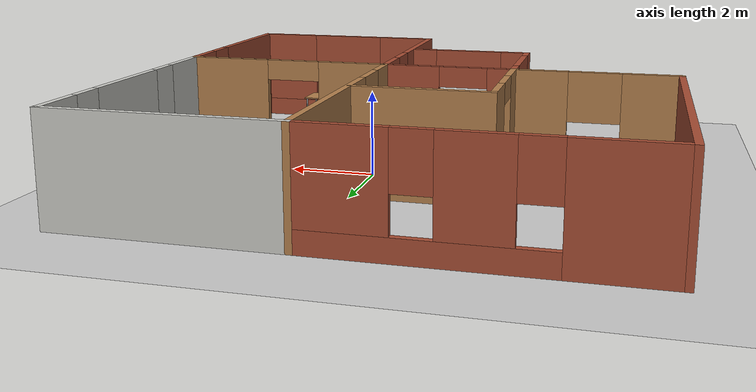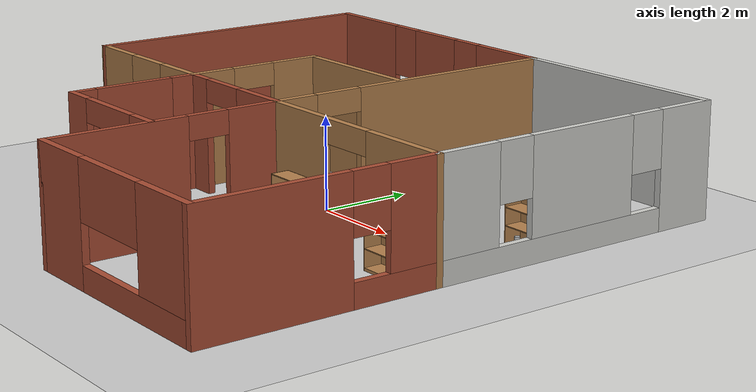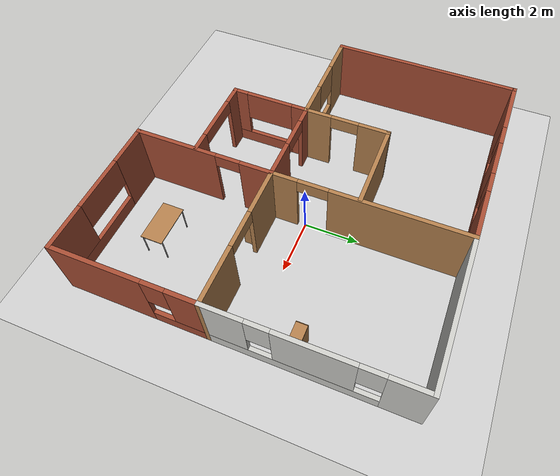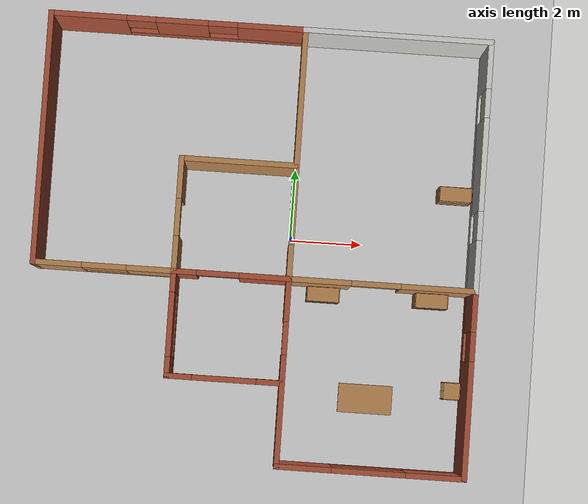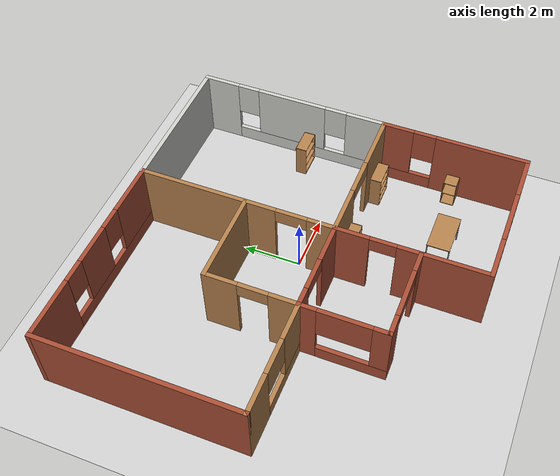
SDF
<sdf version="1.7">
 <world name="default">
  <light name="sun" type="directional">
   <pose>0 0 10 0 -0 0</pose>
   <diffuse>0.8 0.8 0.8 1</diffuse>
   <specular>0.2 0.2 0.2 1</specular>
   <attenuation>
    <range>1000</range>
    <constant>0.9</constant>
    <linear>0.01</linear>
    <quadratic>0.001</quadratic>
   </attenuation>
   <direction>-0.5 0.1 -0.9</direction>
   <spot><inner_angle>0</inner_angle><outer_angle>0</outer_angle><falloff>0</falloff></spot>
  </light>
  <model name="ground_plane">
   <static>1</static>
   <link name="link">
    <collision name="collision">
     <geometry><plane><normal>0 0 1</normal><size>100 100</size></plane></geometry>
     <surface>
      <contact><collide_bitmask>65535</collide_bitmask></contact>
      <friction><ode><mu>100</mu><mu2>50</mu2></ode></friction>
     </surface>
    </collision>
    <visual name="visual">
     <cast_shadows>0</cast_shadows>
     <geometry><plane><normal>0 0 1</normal><size>100 100</size></plane></geometry>
     <material>
      <script><uri>file://media/materials/scripts/gazebo.material</uri><name>Gazebo/Grey</name></script>
     </material>
    </visual>
   </link>
  </model>
  <gravity>0 0 -9.8</gravity>
  <magnetic_field>6e-06 2.3e-05 -4.2e-05</magnetic_field>
  <atmosphere type="adiabatic"/>
  <physics type="ode">
   <max_step_size>0.001</max_step_size>
   <real_time_factor>1</real_time_factor>
   <real_time_update_rate>1000</real_time_update_rate>
  </physics>
  <scene><ambient>0.4 0.4 0.4 1</ambient><background>0.7 0.7 0.7 1</background><shadows>0</shadows></scene>
  <spherical_coordinates>
   <surface_model>EARTH_WGS84</surface_model>
   <latitude_deg>0</latitude_deg>
   <longitude_deg>0</longitude_deg>
   <elevation>0</elevation>
   <heading_deg>0</heading_deg>
  </spherical_coordinates>
  <model name="bookshelf">
   <static>1</static>
   <link name="link">
    <inertial><mass>1</mass></inertial>
    <collision name="back">
     <pose>0 0.005 0.6 0 -0 0</pose>
     <geometry><box><size>0.9 0.01 1.2</size></box></geometry>
    </collision>
    <visual name="visual1">
     <pose>0 0.005 0.6 0 -0 0</pose>
     <geometry><box><size>0.9 0.01 1.2</size></box></geometry>
     <material>
      <script><uri>file://media/materials/scripts/gazebo.material</uri><name>Gazebo/Wood</name></script>
     </material>
    </visual>
    <collision name="left_side">
     <pose>0.45 -0.195 0.6 0 -0 0</pose>
     <geometry><box><size>0.02 0.4 1.2</size></box></geometry>
    </collision>
    <visual name="visual2">
     <pose>0.45 -0.195 0.6 0 -0 0</pose>
     <geometry><box><size>0.02 0.4 1.2</size></box></geometry>
     <material>
      <script><uri>file://media/materials/scripts/gazebo.material</uri><name>Gazebo/Wood</name></script>
     </material>
    </visual>
    <collision name="right_side">
     <pose>-0.45 -0.195 0.6 0 -0 0</pose>
     <geometry><box><size>0.02 0.4 1.2</size></box></geometry>
    </collision>
    <visual name="visual3">
     <pose>-0.45 -0.195 0.6 0 -0 0</pose>
     <geometry><box><size>0.02 0.4 1.2</size></box></geometry>
     <material>
      <script><uri>file://media/materials/scripts/gazebo.material</uri><name>Gazebo/Wood</name></script>
     </material>
    </visual>
    <collision name="bottom">
     <pose>0 -0.195 0.03 0 -0 0</pose>
     <geometry><box><size>0.88 0.4 0.06</size></box></geometry>
    </collision>
    <visual name="visual4">
     <pose>0 -0.195 0.03 0 -0 0</pose>
     <geometry><box><size>0.88 0.4 0.06</size></box></geometry>
     <material>
      <script><uri>file://media/materials/scripts/gazebo.material</uri><name>Gazebo/Wood</name></script>
     </material>
    </visual>
    <collision name="top">
     <pose>0 -0.195 1.19 0 -0 0</pose>
     <geometry><box><size>0.88 0.4 0.02</size></box></geometry>
    </collision>
    <visual name="visual5">
     <pose>0 -0.195 1.19 0 -0 0</pose>
     <geometry><box><size>0.88 0.4 0.02</size></box></geometry>
     <material>
      <script><uri>file://media/materials/scripts/gazebo.material</uri><name>Gazebo/Wood</name></script>
     </material>
    </visual>
    <collision name="low_shelf">
     <pose>0 -0.195 0.43 0 -0 0</pose>
     <geometry><box><size>0.88 0.4 0.02</size></box></geometry>
    </collision>
    <visual name="visual6">
     <pose>0 -0.195 0.43 0 -0 0</pose>
     <geometry><box><size>0.88 0.4 0.02</size></box></geometry>
     <material>
      <script><uri>file://media/materials/scripts/gazebo.material</uri><name>Gazebo/Wood</name></script>
     </material>
    </visual>
    <collision name="high_shelf">
     <pose>0 -0.195 0.8 0 -0 0</pose>
     <geometry><box><size>0.88 0.4 0.02</size></box></geometry>
    </collision>
    <visual name="visual7">
     <pose>0 -0.195 0.8 0 -0 0</pose>
     <geometry><box><size>0.88 0.4 0.02</size></box></geometry>
     <material>
      <script><uri>file://media/materials/scripts/gazebo.material</uri><name>Gazebo/Wood</name></script>
     </material>
    </visual>
   </link>
   <pose>0.993813 -1.31372 0 0 -0 0</pose>
  </model>
  <model name="bookshelf_0">
   <static>1</static>
   <link name="link">
    <inertial><mass>1</mass></inertial>
    <collision name="back">
     <pose>0 0.005 0.6 0 -0 0</pose>
     <geometry><box><size>0.9 0.01 1.2</size></box></geometry>
    </collision>
    <visual name="visual1">
     <pose>0 0.005 0.6 0 -0 0</pose>
     <geometry><box><size>0.9 0.01 1.2</size></box></geometry>
     <material>
      <script><uri>file://media/materials/scripts/gazebo.material</uri><name>Gazebo/Wood</name></script>
     </material>
    </visual>
    <collision name="left_side">
     <pose>0.45 -0.195 0.6 0 -0 0</pose>
     <geometry><box><size>0.02 0.4 1.2</size></box></geometry>
    </collision>
    <visual name="visual2">
     <pose>0.45 -0.195 0.6 0 -0 0</pose>
     <geometry><box><size>0.02 0.4 1.2</size></box></geometry>
     <material>
      <script><uri>file://media/materials/scripts/gazebo.material</uri><name>Gazebo/Wood</name></script>
     </material>
    </visual>
    <collision name="right_side">
     <pose>-0.45 -0.195 0.6 0 -0 0</pose>
     <geometry><box><size>0.02 0.4 1.2</size></box></geometry>
    </collision>
    <visual name="visual3">
     <pose>-0.45 -0.195 0.6 0 -0 0</pose>
     <geometry><box><size>0.02 0.4 1.2</size></box></geometry>
     <material>
      <script><uri>file://media/materials/scripts/gazebo.material</uri><name>Gazebo/Wood</name></script>
     </material>
    </visual>
    <collision name="bottom">
     <pose>0 -0.195 0.03 0 -0 0</pose>
     <geometry><box><size>0.88 0.4 0.06</size></box></geometry>
    </collision>
    <visual name="visual4">
     <pose>0 -0.195 0.03 0 -0 0</pose>
     <geometry><box><size>0.88 0.4 0.06</size></box></geometry>
     <material>
      <script><uri>file://media/materials/scripts/gazebo.material</uri><name>Gazebo/Wood</name></script>
     </material>
    </visual>
    <collision name="top">
     <pose>0 -0.195 1.19 0 -0 0</pose>
     <geometry><box><size>0.88 0.4 0.02</size></box></geometry>
    </collision>
    <visual name="visual5">
     <pose>0 -0.195 1.19 0 -0 0</pose>
     <geometry><box><size>0.88 0.4 0.02</size></box></geometry>
     <material>
      <script><uri>file://media/materials/scripts/gazebo.material</uri><name>Gazebo/Wood</name></script>
     </material>
    </visual>
    <collision name="low_shelf">
     <pose>0 -0.195 0.43 0 -0 0</pose>
     <geometry><box><size>0.88 0.4 0.02</size></box></geometry>
    </collision>
    <visual name="visual6">
     <pose>0 -0.195 0.43 0 -0 0</pose>
     <geometry><box><size>0.88 0.4 0.02</size></box></geometry>
     <material>
      <script><uri>file://media/materials/scripts/gazebo.material</uri><name>Gazebo/Wood</name></script>
     </material>
    </visual>
    <collision name="high_shelf">
     <pose>0 -0.195 0.8 0 -0 0</pose>
     <geometry><box><size>0.88 0.4 0.02</size></box></geometry>
    </collision>
    <visual name="visual7">
     <pose>0 -0.195 0.8 0 -0 0</pose>
     <geometry><box><size>0.88 0.4 0.02</size></box></geometry>
     <material>
      <script><uri>file://media/materials/scripts/gazebo.material</uri><name>Gazebo/Wood</name></script>
     </material>
    </visual>
   </link>
   <pose>4.0161 -1.29459 0 0 -0 0</pose>
  </model>
  <model name="cabinet">
   <static>1</static>
   <link name="cabinet_bottom_plate">
    <inertial>
     <pose>0 0 -1 0 -0 0</pose>
     <inertia><ixx>2.05</ixx><ixy>0</ixy><ixz>0</ixz><iyy>2.05</iyy><iyz>0</iyz><izz>2.05</izz></inertia>
     <mass>25</mass>
    </inertial>
    <collision name="cabinet_bottom_plate_geom">
     <pose>0 0 0.01 0 -0 0</pose>
     <geometry><box><size>0.45 0.45 0.02</size></box></geometry>
    </collision>
    <visual name="cabinet_bottom_plate_geom_visual">
     <pose>0 0 0.01 0 -0 0</pose>
     <geometry><box><size>0.45 0.45 0.02</size></box></geometry>
     <material>
      <script><uri>file://media/materials/scripts/gazebo.material</uri><name>Gazebo/Wood</name></script>
     </material>
    </visual>
    <collision name="cabinet_bottom_plate_geom_cabinet_back_plate">
     <pose>0.235 0 0.51 0 -0 0</pose>
     <geometry><box><size>0.02 0.45 1.02</size></box></geometry>
    </collision>
    <visual name="cabinet_bottom_plate_geom_cabinet_back_plate_visual">
     <pose>0.235 0 0.51 0 -0 0</pose>
     <geometry><box><size>0.02 0.45 1.02</size></box></geometry>
     <material>
      <script><uri>file://media/materials/scripts/gazebo.material</uri><name>Gazebo/Wood</name></script>
     </material>
    </visual>
    <collision name="cabinet_bottom_plate_geom_cabinet_left_plate">
     <pose>0 0.235 0.51 0 -0 0</pose>
     <geometry><box><size>0.45 0.02 1.02</size></box></geometry>
    </collision>
    <visual name="cabinet_bottom_plate_geom_cabinet_left_plate_visual">
     <pose>0 0.235 0.51 0 -0 0</pose>
     <geometry><box><size>0.45 0.02 1.02</size></box></geometry>
     <material>
      <script><uri>file://media/materials/scripts/gazebo.material</uri><name>Gazebo/Wood</name></script>
     </material>
    </visual>
    <collision name="cabinet_bottom_plate_geom_cabinet_middle_plate">
     <pose>0 0 0.51 0 -0 0</pose>
     <geometry><box><size>0.45 0.45 0.02</size></box></geometry>
    </collision>
    <visual name="cabinet_bottom_plate_geom_cabinet_middle_plate_visual">
     <pose>0 0 0.51 0 -0 0</pose>
     <geometry><box><size>0.45 0.45 0.02</size></box></geometry>
     <material>
      <script><uri>file://media/materials/scripts/gazebo.material</uri><name>Gazebo/Wood</name></script>
     </material>
    </visual>
    <collision name="cabinet_bottom_plate_geom_cabinet_right_plate">
     <pose>0 -0.235 0.51 0 -0 0</pose>
     <geometry><box><size>0.45 0.02 1.02</size></box></geometry>
    </collision>
    <visual name="cabinet_bottom_plate_geom_cabinet_right_plate_visual">
     <pose>0 -0.235 0.51 0 -0 0</pose>
     <geometry><box><size>0.45 0.02 1.02</size></box></geometry>
     <material>
      <script><uri>file://media/materials/scripts/gazebo.material</uri><name>Gazebo/Wood</name></script>
     </material>
    </visual>
    <collision name="cabinet_bottom_plate_geom_cabinet_top_plate">
     <pose>0 0 1.01 0 -0 0</pose>
     <geometry><box><size>0.45 0.45 0.02</size></box></geometry>
    </collision>
    <visual name="cabinet_bottom_plate_geom_cabinet_top_plate_visual">
     <pose>0 0 1.01 0 -0 0</pose>
     <geometry><box><size>0.45 0.45 0.02</size></box></geometry>
     <material>
      <script><uri>file://media/materials/scripts/gazebo.material</uri><name>Gazebo/Wood</name></script>
     </material>
    </visual>
   </link>
   <pose>4.74463 -3.94895 0 0 -0 0</pose>
  </model>
  <model name="basic_house_model">
   <link name="Wall_13">
    <pose>-6.05 2.55 0 0 0 -1.5708</pose>
    <visual name="Wall_13_Visual">
     <pose>0 0 1.25 0 -0 0</pose>
     <geometry><box><size>7 0.15 2.5</size></box></geometry>
     <material>
      <script><uri>file://media/materials/scripts/gazebo.material</uri><name>Gazebo/Bricks</name></script>
      <ambient>1 1 1 1</ambient>
      <shader type="pixel"/>
     </material>
     <meta><layer>0</layer></meta>
    </visual>
    <collision name="Wall_13_Collision">
     <pose>0 0 1.25 0 -0 0</pose>
     <geometry><box><size>7 0.15 2.5</size></box></geometry>
     <surface>
      <friction>
       <ode><mu>1</mu><mu2>1</mu2><fdir1>0 0 0</fdir1><slip1>0</slip1><slip2>0</slip2></ode>
       <torsional>
        <coefficient>1</coefficient>
        <patch_radius>0</patch_radius>
        <surface_radius>0</surface_radius>
        <use_patch_radius>1</use_patch_radius>
        <ode><slip>0</slip></ode>
       </torsional>
      </friction>
      <bounce><restitution_coefficient>0</restitution_coefficient><threshold>1e+06</threshold></bounce>
      <contact>
       <collide_without_contact>0</collide_without_contact>
       <collide_without_contact_bitmask>1</collide_without_contact_bitmask>
       <collide_bitmask>1</collide_bitmask>
       <ode>
        <soft_cfm>0</soft_cfm>
        <soft_erp>0.2</soft_erp>
        <kp>1e+13</kp>
        <kd>1</kd>
        <max_vel>0.01</max_vel>
        <min_depth>0</min_depth>
       </ode>
       <bullet>
        <split_impulse>1</split_impulse>
        <split_impulse_penetration_threshold>-0.01</split_impulse_penetration_threshold>
        <soft_cfm>0</soft_cfm>
        <soft_erp>0.2</soft_erp>
        <kp>1e+13</kp>
        <kd>1</kd>
       </bullet>
      </contact>
     </surface>
    </collision>
   </link>
   <link name="Wall_14">
    <pose>-4.125 -0.875 0 0 -0 0</pose>
    <visual name="Wall_14_Visual_0">
     <pose>-1.30014 0 1.25 0 -0 0</pose>
     <geometry><box><size>1.39972 0.15 2.5</size></box></geometry>
     <material>
      <script><uri>file://media/materials/scripts/gazebo.material</uri><name>Gazebo/Wood</name></script>
      <ambient>1 1 1 1</ambient>
      <shader type="pixel"/>
     </material>
     <meta><layer>0</layer></meta>
    </visual>
    <visual name="Wall_14_Visual_1">
     <pose>0.699859 0 0.25 0 -0 0</pose>
     <geometry><box><size>2.60028 0.15 0.5</size></box></geometry>
     <material>
      <script><uri>file://media/materials/scripts/gazebo.material</uri><name>Gazebo/Wood</name></script>
      <ambient>1 1 1 1</ambient>
      <shader type="pixel"/>
     </material>
     <meta><layer>0</layer></meta>
    </visual>
    <visual name="Wall_14_Visual_2">
     <pose>1.31418 0 1.5 0 -0 0</pose>
     <geometry><box><size>1.37164 0.15 2</size></box></geometry>
     <material>
      <script><uri>file://media/materials/scripts/gazebo.material</uri><name>Gazebo/Wood</name></script>
      <ambient>1 1 1 1</ambient>
      <shader type="pixel"/>
     </material>
     <meta><layer>0</layer></meta>
    </visual>
    <visual name="Wall_14_Visual_3">
     <pose>0.014039 0 1.9 0 -0 0</pose>
     <geometry><box><size>1.22864 0.15 1.2</size></box></geometry>
     <material>
      <script><uri>file://media/materials/scripts/gazebo.material</uri><name>Gazebo/Wood</name></script>
      <ambient>1 1 1 1</ambient>
      <shader type="pixel"/>
     </material>
     <meta><layer>0</layer></meta>
    </visual>
    <collision name="Wall_14_Collision_0">
     <pose>-1.30014 0 1.25 0 -0 0</pose>
     <geometry><box><size>1.39972 0.15 2.5</size></box></geometry>
     <surface>
      <friction>
       <ode><mu>1</mu><mu2>1</mu2><fdir1>0 0 0</fdir1><slip1>0</slip1><slip2>0</slip2></ode>
       <torsional>
        <coefficient>1</coefficient>
        <patch_radius>0</patch_radius>
        <surface_radius>0</surface_radius>
        <use_patch_radius>1</use_patch_radius>
        <ode><slip>0</slip></ode>
       </torsional>
      </friction>
      <bounce><restitution_coefficient>0</restitution_coefficient><threshold>1e+06</threshold></bounce>
      <contact>
       <collide_without_contact>0</collide_without_contact>
       <collide_without_contact_bitmask>1</collide_without_contact_bitmask>
       <collide_bitmask>1</collide_bitmask>
       <ode>
        <soft_cfm>0</soft_cfm>
        <soft_erp>0.2</soft_erp>
        <kp>1e+13</kp>
        <kd>1</kd>
        <max_vel>0.01</max_vel>
        <min_depth>0</min_depth>
       </ode>
       <bullet>
        <split_impulse>1</split_impulse>
        <split_impulse_penetration_threshold>-0.01</split_impulse_penetration_threshold>
        <soft_cfm>0</soft_cfm>
        <soft_erp>0.2</soft_erp>
        <kp>1e+13</kp>
        <kd>1</kd>
       </bullet>
      </contact>
     </surface>
    </collision>
    <collision name="Wall_14_Collision_1">
     <pose>0.699859 0 0.25 0 -0 0</pose>
     <geometry><box><size>2.60028 0.15 0.5</size></box></geometry>
     <surface>
      <friction>
       <ode><mu>1</mu><mu2>1</mu2><fdir1>0 0 0</fdir1><slip1>0</slip1><slip2>0</slip2></ode>
       <torsional>
        <coefficient>1</coefficient>
        <patch_radius>0</patch_radius>
        <surface_radius>0</surface_radius>
        <use_patch_radius>1</use_patch_radius>
        <ode><slip>0</slip></ode>
       </torsional>
      </friction>
      <bounce><restitution_coefficient>0</restitution_coefficient><threshold>1e+06</threshold></bounce>
      <contact>
       <collide_without_contact>0</collide_without_contact>
       <collide_without_contact_bitmask>1</collide_without_contact_bitmask>
       <collide_bitmask>1</collide_bitmask>
       <ode>
        <soft_cfm>0</soft_cfm>
        <soft_erp>0.2</soft_erp>
        <kp>1e+13</kp>
        <kd>1</kd>
        <max_vel>0.01</max_vel>
        <min_depth>0</min_depth>
       </ode>
       <bullet>
        <split_impulse>1</split_impulse>
        <split_impulse_penetration_threshold>-0.01</split_impulse_penetration_threshold>
        <soft_cfm>0</soft_cfm>
        <soft_erp>0.2</soft_erp>
        <kp>1e+13</kp>
        <kd>1</kd>
       </bullet>
      </contact>
     </surface>
    </collision>
    <collision name="Wall_14_Collision_2">
     <pose>1.31418 0 1.5 0 -0 0</pose>
     <geometry><box><size>1.37164 0.15 2</size></box></geometry>
     <surface>
      <friction>
       <ode><mu>1</mu><mu2>1</mu2><fdir1>0 0 0</fdir1><slip1>0</slip1><slip2>0</slip2></ode>
       <torsional>
        <coefficient>1</coefficient>
        <patch_radius>0</patch_radius>
        <surface_radius>0</surface_radius>
        <use_patch_radius>1</use_patch_radius>
        <ode><slip>0</slip></ode>
       </torsional>
      </friction>
      <bounce><restitution_coefficient>0</restitution_coefficient><threshold>1e+06</threshold></bounce>
      <contact>
       <collide_without_contact>0</collide_without_contact>
       <collide_without_contact_bitmask>1</collide_without_contact_bitmask>
       <collide_bitmask>1</collide_bitmask>
       <ode>
        <soft_cfm>0</soft_cfm>
        <soft_erp>0.2</soft_erp>
        <kp>1e+13</kp>
        <kd>1</kd>
        <max_vel>0.01</max_vel>
        <min_depth>0</min_depth>
       </ode>
       <bullet>
        <split_impulse>1</split_impulse>
        <split_impulse_penetration_threshold>-0.01</split_impulse_penetration_threshold>
        <soft_cfm>0</soft_cfm>
        <soft_erp>0.2</soft_erp>
        <kp>1e+13</kp>
        <kd>1</kd>
       </bullet>
      </contact>
     </surface>
    </collision>
    <collision name="Wall_14_Collision_3">
     <pose>0.014039 0 1.9 0 -0 0</pose>
     <geometry><box><size>1.22864 0.15 1.2</size></box></geometry>
     <surface>
      <friction>
       <ode><mu>1</mu><mu2>1</mu2><fdir1>0 0 0</fdir1><slip1>0</slip1><slip2>0</slip2></ode>
       <torsional>
        <coefficient>1</coefficient>
        <patch_radius>0</patch_radius>
        <surface_radius>0</surface_radius>
        <use_patch_radius>1</use_patch_radius>
        <ode><slip>0</slip></ode>
       </torsional>
      </friction>
      <bounce><restitution_coefficient>0</restitution_coefficient><threshold>1e+06</threshold></bounce>
      <contact>
       <collide_without_contact>0</collide_without_contact>
       <collide_without_contact_bitmask>1</collide_without_contact_bitmask>
       <collide_bitmask>1</collide_bitmask>
       <ode>
        <soft_cfm>0</soft_cfm>
        <soft_erp>0.2</soft_erp>
        <kp>1e+13</kp>
        <kd>1</kd>
        <max_vel>0.01</max_vel>
        <min_depth>0</min_depth>
       </ode>
       <bullet>
        <split_impulse>1</split_impulse>
        <split_impulse_penetration_threshold>-0.01</split_impulse_penetration_threshold>
        <soft_cfm>0</soft_cfm>
        <soft_erp>0.2</soft_erp>
        <kp>1e+13</kp>
        <kd>1</kd>
       </bullet>
      </contact>
     </surface>
    </collision>
   </link>
   <link name="Wall_15">
    <pose>-2.2 0.675 0 0 -0 1.5708</pose>
    <visual name="Wall_15_Visual_0">
     <pose>-1.10266 0 1.25 0 -0 0</pose>
     <geometry><box><size>1.04468 0.15 2.5</size></box></geometry>
     <material>
      <script><uri>file://media/materials/scripts/gazebo.material</uri><name>Gazebo/Wood</name></script>
      <ambient>1 1 1 1</ambient>
      <shader type="pixel"/>
     </material>
     <meta><layer>0</layer></meta>
    </visual>
    <visual name="Wall_15_Visual_1">
     <pose>1.03215 0 1.25 0 -0 0</pose>
     <geometry><box><size>1.1857 0.15 2.5</size></box></geometry>
     <material>
      <script><uri>file://media/materials/scripts/gazebo.material</uri><name>Gazebo/Wood</name></script>
      <ambient>1 1 1 1</ambient>
      <shader type="pixel"/>
     </material>
     <meta><layer>0</layer></meta>
    </visual>
    <visual name="Wall_15_Visual_2">
     <pose>-0.070509 0 2.25 0 -0 0</pose>
     <geometry><box><size>1.01962 0.15 0.5</size></box></geometry>
     <material>
      <script><uri>file://media/materials/scripts/gazebo.material</uri><name>Gazebo/Wood</name></script>
      <ambient>1 1 1 1</ambient>
      <shader type="pixel"/>
     </material>
     <meta><layer>0</layer></meta>
    </visual>
    <collision name="Wall_15_Collision_0">
     <pose>-1.10266 0 1.25 0 -0 0</pose>
     <geometry><box><size>1.04468 0.15 2.5</size></box></geometry>
     <surface>
      <friction>
       <ode><mu>1</mu><mu2>1</mu2><fdir1>0 0 0</fdir1><slip1>0</slip1><slip2>0</slip2></ode>
       <torsional>
        <coefficient>1</coefficient>
        <patch_radius>0</patch_radius>
        <surface_radius>0</surface_radius>
        <use_patch_radius>1</use_patch_radius>
        <ode><slip>0</slip></ode>
       </torsional>
      </friction>
      <bounce><restitution_coefficient>0</restitution_coefficient><threshold>1e+06</threshold></bounce>
      <contact>
       <collide_without_contact>0</collide_without_contact>
       <collide_without_contact_bitmask>1</collide_without_contact_bitmask>
       <collide_bitmask>1</collide_bitmask>
       <ode>
        <soft_cfm>0</soft_cfm>
        <soft_erp>0.2</soft_erp>
        <kp>1e+13</kp>
        <kd>1</kd>
        <max_vel>0.01</max_vel>
        <min_depth>0</min_depth>
       </ode>
       <bullet>
        <split_impulse>1</split_impulse>
        <split_impulse_penetration_threshold>-0.01</split_impulse_penetration_threshold>
        <soft_cfm>0</soft_cfm>
        <soft_erp>0.2</soft_erp>
        <kp>1e+13</kp>
        <kd>1</kd>
       </bullet>
      </contact>
     </surface>
    </collision>
    <collision name="Wall_15_Collision_1">
     <pose>1.03215 0 1.25 0 -0 0</pose>
     <geometry><box><size>1.1857 0.15 2.5</size></box></geometry>
     <surface>
      <friction>
       <ode><mu>1</mu><mu2>1</mu2><fdir1>0 0 0</fdir1><slip1>0</slip1><slip2>0</slip2></ode>
       <torsional>
        <coefficient>1</coefficient>
        <patch_radius>0</patch_radius>
        <surface_radius>0</surface_radius>
        <use_patch_radius>1</use_patch_radius>
        <ode><slip>0</slip></ode>
       </torsional>
      </friction>
      <bounce><restitution_coefficient>0</restitution_coefficient><threshold>1e+06</threshold></bounce>
      <contact>
       <collide_without_contact>0</collide_without_contact>
       <collide_without_contact_bitmask>1</collide_without_contact_bitmask>
       <collide_bitmask>1</collide_bitmask>
       <ode>
        <soft_cfm>0</soft_cfm>
        <soft_erp>0.2</soft_erp>
        <kp>1e+13</kp>
        <kd>1</kd>
        <max_vel>0.01</max_vel>
        <min_depth>0</min_depth>
       </ode>
       <bullet>
        <split_impulse>1</split_impulse>
        <split_impulse_penetration_threshold>-0.01</split_impulse_penetration_threshold>
        <soft_cfm>0</soft_cfm>
        <soft_erp>0.2</soft_erp>
        <kp>1e+13</kp>
        <kd>1</kd>
       </bullet>
      </contact>
     </surface>
    </collision>
    <collision name="Wall_15_Collision_2">
     <pose>-0.070509 0 2.25 0 -0 0</pose>
     <geometry><box><size>1.01962 0.15 0.5</size></box></geometry>
     <surface>
      <friction>
       <ode><mu>1</mu><mu2>1</mu2><fdir1>0 0 0</fdir1><slip1>0</slip1><slip2>0</slip2></ode>
       <torsional>
        <coefficient>1</coefficient>
        <patch_radius>0</patch_radius>
        <surface_radius>0</surface_radius>
        <use_patch_radius>1</use_patch_radius>
        <ode><slip>0</slip></ode>
       </torsional>
      </friction>
      <bounce><restitution_coefficient>0</restitution_coefficient><threshold>1e+06</threshold></bounce>
      <contact>
       <collide_without_contact>0</collide_without_contact>
       <collide_without_contact_bitmask>1</collide_without_contact_bitmask>
       <collide_bitmask>1</collide_bitmask>
       <ode>
        <soft_cfm>0</soft_cfm>
        <soft_erp>0.2</soft_erp>
        <kp>1e+13</kp>
        <kd>1</kd>
        <max_vel>0.01</max_vel>
        <min_depth>0</min_depth>
       </ode>
       <bullet>
        <split_impulse>1</split_impulse>
        <split_impulse_penetration_threshold>-0.01</split_impulse_penetration_threshold>
        <soft_cfm>0</soft_cfm>
        <soft_erp>0.2</soft_erp>
        <kp>1e+13</kp>
        <kd>1</kd>
       </bullet>
      </contact>
     </surface>
    </collision>
   </link>
   <link name="Wall_16">
    <pose>-0.65 2.225 0 0 -0 0</pose>
    <visual name="Wall_16_Visual">
     <pose>0 0 1.25 0 -0 0</pose>
     <geometry><box><size>3.25 0.15 2.5</size></box></geometry>
     <material>
      <script><uri>file://media/materials/scripts/gazebo.material</uri><name>Gazebo/Wood</name></script>
      <ambient>1 1 1 1</ambient>
      <shader type="pixel"/>
     </material>
     <meta><layer>0</layer></meta>
    </visual>
    <collision name="Wall_16_Collision">
     <pose>0 0 1.25 0 -0 0</pose>
     <geometry><box><size>3.25 0.15 2.5</size></box></geometry>
     <surface>
      <friction>
       <ode><mu>1</mu><mu2>1</mu2><fdir1>0 0 0</fdir1><slip1>0</slip1><slip2>0</slip2></ode>
       <torsional>
        <coefficient>1</coefficient>
        <patch_radius>0</patch_radius>
        <surface_radius>0</surface_radius>
        <use_patch_radius>1</use_patch_radius>
        <ode><slip>0</slip></ode>
       </torsional>
      </friction>
      <bounce><restitution_coefficient>0</restitution_coefficient><threshold>1e+06</threshold></bounce>
      <contact>
       <collide_without_contact>0</collide_without_contact>
       <collide_without_contact_bitmask>1</collide_without_contact_bitmask>
       <collide_bitmask>1</collide_bitmask>
       <ode>
        <soft_cfm>0</soft_cfm>
        <soft_erp>0.2</soft_erp>
        <kp>1e+13</kp>
        <kd>1</kd>
        <max_vel>0.01</max_vel>
        <min_depth>0</min_depth>
       </ode>
       <bullet>
        <split_impulse>1</split_impulse>
        <split_impulse_penetration_threshold>-0.01</split_impulse_penetration_threshold>
        <soft_cfm>0</soft_cfm>
        <soft_erp>0.2</soft_erp>
        <kp>1e+13</kp>
        <kd>1</kd>
       </bullet>
      </contact>
     </surface>
    </collision>
   </link>
   <link name="Wall_18">
    <pose>-0.625 -0.875 0 0 -0 0</pose>
    <visual name="Wall_18_Visual_0">
     <pose>-1.3026 0 1.25 0 -0 0</pose>
     <geometry><box><size>0.694802 0.15 2.5</size></box></geometry>
     <material>
      <script><uri>file://media/materials/scripts/gazebo.material</uri><name>Gazebo/Bricks</name></script>
      <ambient>1 1 1 1</ambient>
      <shader type="pixel"/>
     </material>
     <meta><layer>0</layer></meta>
    </visual>
    <visual name="Wall_18_Visual_1">
     <pose>0.929233 0 1.25 0 -0 0</pose>
     <geometry><box><size>1.44153 0.15 2.5</size></box></geometry>
     <material>
      <script><uri>file://media/materials/scripts/gazebo.material</uri><name>Gazebo/Bricks</name></script>
      <ambient>1 1 1 1</ambient>
      <shader type="pixel"/>
     </material>
     <meta><layer>0</layer></meta>
    </visual>
    <visual name="Wall_18_Visual_2">
     <pose>-0.373366 0 2.25 0 -0 0</pose>
     <geometry><box><size>1.16366 0.15 0.5</size></box></geometry>
     <material>
      <script><uri>file://media/materials/scripts/gazebo.material</uri><name>Gazebo/Bricks</name></script>
      <ambient>1 1 1 1</ambient>
      <shader type="pixel"/>
     </material>
     <meta><layer>0</layer></meta>
    </visual>
    <collision name="Wall_18_Collision_0">
     <pose>-1.3026 0 1.25 0 -0 0</pose>
     <geometry><box><size>0.694802 0.15 2.5</size></box></geometry>
     <surface>
      <friction>
       <ode><mu>1</mu><mu2>1</mu2><fdir1>0 0 0</fdir1><slip1>0</slip1><slip2>0</slip2></ode>
       <torsional>
        <coefficient>1</coefficient>
        <patch_radius>0</patch_radius>
        <surface_radius>0</surface_radius>
        <use_patch_radius>1</use_patch_radius>
        <ode><slip>0</slip></ode>
       </torsional>
      </friction>
      <bounce><restitution_coefficient>0</restitution_coefficient><threshold>1e+06</threshold></bounce>
      <contact>
       <collide_without_contact>0</collide_without_contact>
       <collide_without_contact_bitmask>1</collide_without_contact_bitmask>
       <collide_bitmask>1</collide_bitmask>
       <ode>
        <soft_cfm>0</soft_cfm>
        <soft_erp>0.2</soft_erp>
        <kp>1e+13</kp>
        <kd>1</kd>
        <max_vel>0.01</max_vel>
        <min_depth>0</min_depth>
       </ode>
       <bullet>
        <split_impulse>1</split_impulse>
        <split_impulse_penetration_threshold>-0.01</split_impulse_penetration_threshold>
        <soft_cfm>0</soft_cfm>
        <soft_erp>0.2</soft_erp>
        <kp>1e+13</kp>
        <kd>1</kd>
       </bullet>
      </contact>
     </surface>
    </collision>
    <collision name="Wall_18_Collision_1">
     <pose>0.929233 0 1.25 0 -0 0</pose>
     <geometry><box><size>1.44153 0.15 2.5</size></box></geometry>
     <surface>
      <friction>
       <ode><mu>1</mu><mu2>1</mu2><fdir1>0 0 0</fdir1><slip1>0</slip1><slip2>0</slip2></ode>
       <torsional>
        <coefficient>1</coefficient>
        <patch_radius>0</patch_radius>
        <surface_radius>0</surface_radius>
        <use_patch_radius>1</use_patch_radius>
        <ode><slip>0</slip></ode>
       </torsional>
      </friction>
      <bounce><restitution_coefficient>0</restitution_coefficient><threshold>1e+06</threshold></bounce>
      <contact>
       <collide_without_contact>0</collide_without_contact>
       <collide_without_contact_bitmask>1</collide_without_contact_bitmask>
       <collide_bitmask>1</collide_bitmask>
       <ode>
        <soft_cfm>0</soft_cfm>
        <soft_erp>0.2</soft_erp>
        <kp>1e+13</kp>
        <kd>1</kd>
        <max_vel>0.01</max_vel>
        <min_depth>0</min_depth>
       </ode>
       <bullet>
        <split_impulse>1</split_impulse>
        <split_impulse_penetration_threshold>-0.01</split_impulse_penetration_threshold>
        <soft_cfm>0</soft_cfm>
        <soft_erp>0.2</soft_erp>
        <kp>1e+13</kp>
        <kd>1</kd>
       </bullet>
      </contact>
     </surface>
    </collision>
    <collision name="Wall_18_Collision_2">
     <pose>-0.373366 0 2.25 0 -0 0</pose>
     <geometry><box><size>1.16366 0.15 0.5</size></box></geometry>
     <surface>
      <friction>
       <ode><mu>1</mu><mu2>1</mu2><fdir1>0 0 0</fdir1><slip1>0</slip1><slip2>0</slip2></ode>
       <torsional>
        <coefficient>1</coefficient>
        <patch_radius>0</patch_radius>
        <surface_radius>0</surface_radius>
        <use_patch_radius>1</use_patch_radius>
        <ode><slip>0</slip></ode>
       </torsional>
      </friction>
      <bounce><restitution_coefficient>0</restitution_coefficient><threshold>1e+06</threshold></bounce>
      <contact>
       <collide_without_contact>0</collide_without_contact>
       <collide_without_contact_bitmask>1</collide_without_contact_bitmask>
       <collide_bitmask>1</collide_bitmask>
       <ode>
        <soft_cfm>0</soft_cfm>
        <soft_erp>0.2</soft_erp>
        <kp>1e+13</kp>
        <kd>1</kd>
        <max_vel>0.01</max_vel>
        <min_depth>0</min_depth>
       </ode>
       <bullet>
        <split_impulse>1</split_impulse>
        <split_impulse_penetration_threshold>-0.01</split_impulse_penetration_threshold>
        <soft_cfm>0</soft_cfm>
        <soft_erp>0.2</soft_erp>
        <kp>1e+13</kp>
        <kd>1</kd>
       </bullet>
      </contact>
     </surface>
    </collision>
   </link>
   <link name="Wall_19">
    <pose>0.95 -3.425 0 0 0 -1.5708</pose>
    <visual name="Wall_19_Visual_0">
     <pose>-2.00386 0 1.25 0 -0 0</pose>
     <geometry><box><size>1.24228 0.15 2.5</size></box></geometry>
     <material>
      <script><uri>file://media/materials/scripts/gazebo.material</uri><name>Gazebo/Bricks</name></script>
      <ambient>1 1 1 1</ambient>
      <shader type="pixel"/>
     </material>
     <meta><layer>0</layer></meta>
    </visual>
    <visual name="Wall_19_Visual_1">
     <pose>1.07114 0 1.25 0 -0 0</pose>
     <geometry><box><size>3.10772 0.15 2.5</size></box></geometry>
     <material>
      <script><uri>file://media/materials/scripts/gazebo.material</uri><name>Gazebo/Bricks</name></script>
      <ambient>1 1 1 1</ambient>
      <shader type="pixel"/>
     </material>
     <meta><layer>0</layer></meta>
    </visual>
    <visual name="Wall_19_Visual_2">
     <pose>-0.932718 0 2.25 0 -0 0</pose>
     <geometry><box><size>0.9 0.15 0.5</size></box></geometry>
     <material>
      <script><uri>file://media/materials/scripts/gazebo.material</uri><name>Gazebo/Bricks</name></script>
      <ambient>1 1 1 1</ambient>
      <shader type="pixel"/>
     </material>
     <meta><layer>0</layer></meta>
    </visual>
    <collision name="Wall_19_Collision_0">
     <pose>-2.00386 0 1.25 0 -0 0</pose>
     <geometry><box><size>1.24228 0.15 2.5</size></box></geometry>
     <surface>
      <friction>
       <ode><mu>1</mu><mu2>1</mu2><fdir1>0 0 0</fdir1><slip1>0</slip1><slip2>0</slip2></ode>
       <torsional>
        <coefficient>1</coefficient>
        <patch_radius>0</patch_radius>
        <surface_radius>0</surface_radius>
        <use_patch_radius>1</use_patch_radius>
        <ode><slip>0</slip></ode>
       </torsional>
      </friction>
      <bounce><restitution_coefficient>0</restitution_coefficient><threshold>1e+06</threshold></bounce>
      <contact>
       <collide_without_contact>0</collide_without_contact>
       <collide_without_contact_bitmask>1</collide_without_contact_bitmask>
       <collide_bitmask>1</collide_bitmask>
       <ode>
        <soft_cfm>0</soft_cfm>
        <soft_erp>0.2</soft_erp>
        <kp>1e+13</kp>
        <kd>1</kd>
        <max_vel>0.01</max_vel>
        <min_depth>0</min_depth>
       </ode>
       <bullet>
        <split_impulse>1</split_impulse>
        <split_impulse_penetration_threshold>-0.01</split_impulse_penetration_threshold>
        <soft_cfm>0</soft_cfm>
        <soft_erp>0.2</soft_erp>
        <kp>1e+13</kp>
        <kd>1</kd>
       </bullet>
      </contact>
     </surface>
    </collision>
    <collision name="Wall_19_Collision_1">
     <pose>1.07114 0 1.25 0 -0 0</pose>
     <geometry><box><size>3.10772 0.15 2.5</size></box></geometry>
     <surface>
      <friction>
       <ode><mu>1</mu><mu2>1</mu2><fdir1>0 0 0</fdir1><slip1>0</slip1><slip2>0</slip2></ode>
       <torsional>
        <coefficient>1</coefficient>
        <patch_radius>0</patch_radius>
        <surface_radius>0</surface_radius>
        <use_patch_radius>1</use_patch_radius>
        <ode><slip>0</slip></ode>
       </torsional>
      </friction>
      <bounce><restitution_coefficient>0</restitution_coefficient><threshold>1e+06</threshold></bounce>
      <contact>
       <collide_without_contact>0</collide_without_contact>
       <collide_without_contact_bitmask>1</collide_without_contact_bitmask>
       <collide_bitmask>1</collide_bitmask>
       <ode>
        <soft_cfm>0</soft_cfm>
        <soft_erp>0.2</soft_erp>
        <kp>1e+13</kp>
        <kd>1</kd>
        <max_vel>0.01</max_vel>
        <min_depth>0</min_depth>
       </ode>
       <bullet>
        <split_impulse>1</split_impulse>
        <split_impulse_penetration_threshold>-0.01</split_impulse_penetration_threshold>
        <soft_cfm>0</soft_cfm>
        <soft_erp>0.2</soft_erp>
        <kp>1e+13</kp>
        <kd>1</kd>
       </bullet>
      </contact>
     </surface>
    </collision>
    <collision name="Wall_19_Collision_2">
     <pose>-0.932718 0 2.25 0 -0 0</pose>
     <geometry><box><size>0.9 0.15 0.5</size></box></geometry>
     <surface>
      <friction>
       <ode><mu>1</mu><mu2>1</mu2><fdir1>0 0 0</fdir1><slip1>0</slip1><slip2>0</slip2></ode>
       <torsional>
        <coefficient>1</coefficient>
        <patch_radius>0</patch_radius>
        <surface_radius>0</surface_radius>
        <use_patch_radius>1</use_patch_radius>
        <ode><slip>0</slip></ode>
       </torsional>
      </friction>
      <bounce><restitution_coefficient>0</restitution_coefficient><threshold>1e+06</threshold></bounce>
      <contact>
       <collide_without_contact>0</collide_without_contact>
       <collide_without_contact_bitmask>1</collide_without_contact_bitmask>
       <collide_bitmask>1</collide_bitmask>
       <ode>
        <soft_cfm>0</soft_cfm>
        <soft_erp>0.2</soft_erp>
        <kp>1e+13</kp>
        <kd>1</kd>
        <max_vel>0.01</max_vel>
        <min_depth>0</min_depth>
       </ode>
       <bullet>
        <split_impulse>1</split_impulse>
        <split_impulse_penetration_threshold>-0.01</split_impulse_penetration_threshold>
        <soft_cfm>0</soft_cfm>
        <soft_erp>0.2</soft_erp>
        <kp>1e+13</kp>
        <kd>1</kd>
       </bullet>
      </contact>
     </surface>
    </collision>
   </link>
   <link name="Wall_20">
    <pose>3.5 -5.975 0 0 -0 0</pose>
    <visual name="Wall_20_Visual_0">
     <pose>-1.83971 0 1.25 0 -0 0</pose>
     <geometry><box><size>1.57058 0.15 2.5</size></box></geometry>
     <material>
      <script><uri>file://media/materials/scripts/gazebo.material</uri><name>Gazebo/Bricks</name></script>
      <ambient>1 1 1 1</ambient>
      <shader type="pixel"/>
     </material>
     <meta><layer>0</layer></meta>
    </visual>
    <visual name="Wall_20_Visual_1">
     <pose>0.785288 0 0.25 0 -0 0</pose>
     <geometry><box><size>3.67943 0.15 0.5</size></box></geometry>
     <material>
      <script><uri>file://media/materials/scripts/gazebo.material</uri><name>Gazebo/Bricks</name></script>
      <ambient>1 1 1 1</ambient>
      <shader type="pixel"/>
     </material>
     <meta><layer>0</layer></meta>
    </visual>
    <visual name="Wall_20_Visual_2">
     <pose>1.79171 0 1.5 0 -0 0</pose>
     <geometry><box><size>1.66657 0.15 2</size></box></geometry>
     <material>
      <script><uri>file://media/materials/scripts/gazebo.material</uri><name>Gazebo/Bricks</name></script>
      <ambient>1 1 1 1</ambient>
      <shader type="pixel"/>
     </material>
     <meta><layer>0</layer></meta>
    </visual>
    <visual name="Wall_20_Visual_3">
     <pose>-0.047998 0 1.9 0 -0 0</pose>
     <geometry><box><size>2.01285 0.15 1.2</size></box></geometry>
     <material>
      <script><uri>file://media/materials/scripts/gazebo.material</uri><name>Gazebo/Bricks</name></script>
      <ambient>1 1 1 1</ambient>
      <shader type="pixel"/>
     </material>
     <meta><layer>0</layer></meta>
    </visual>
    <collision name="Wall_20_Collision_0">
     <pose>-1.83971 0 1.25 0 -0 0</pose>
     <geometry><box><size>1.57058 0.15 2.5</size></box></geometry>
     <surface>
      <friction>
       <ode><mu>1</mu><mu2>1</mu2><fdir1>0 0 0</fdir1><slip1>0</slip1><slip2>0</slip2></ode>
       <torsional>
        <coefficient>1</coefficient>
        <patch_radius>0</patch_radius>
        <surface_radius>0</surface_radius>
        <use_patch_radius>1</use_patch_radius>
        <ode><slip>0</slip></ode>
       </torsional>
      </friction>
      <bounce><restitution_coefficient>0</restitution_coefficient><threshold>1e+06</threshold></bounce>
      <contact>
       <collide_without_contact>0</collide_without_contact>
       <collide_without_contact_bitmask>1</collide_without_contact_bitmask>
       <collide_bitmask>1</collide_bitmask>
       <ode>
        <soft_cfm>0</soft_cfm>
        <soft_erp>0.2</soft_erp>
        <kp>1e+13</kp>
        <kd>1</kd>
        <max_vel>0.01</max_vel>
        <min_depth>0</min_depth>
       </ode>
       <bullet>
        <split_impulse>1</split_impulse>
        <split_impulse_penetration_threshold>-0.01</split_impulse_penetration_threshold>
        <soft_cfm>0</soft_cfm>
        <soft_erp>0.2</soft_erp>
        <kp>1e+13</kp>
        <kd>1</kd>
       </bullet>
      </contact>
     </surface>
    </collision>
    <collision name="Wall_20_Collision_2">
     <pose>1.79171 0 1.5 0 -0 0</pose>
     <geometry><box><size>1.66657 0.15 2</size></box></geometry>
     <surface>
      <friction>
       <ode><mu>1</mu><mu2>1</mu2><fdir1>0 0 0</fdir1><slip1>0</slip1><slip2>0</slip2></ode>
       <torsional>
        <coefficient>1</coefficient>
        <patch_radius>0</patch_radius>
        <surface_radius>0</surface_radius>
        <use_patch_radius>1</use_patch_radius>
        <ode><slip>0</slip></ode>
       </torsional>
      </friction>
      <bounce><restitution_coefficient>0</restitution_coefficient><threshold>1e+06</threshold></bounce>
      <contact>
       <collide_without_contact>0</collide_without_contact>
       <collide_without_contact_bitmask>1</collide_without_contact_bitmask>
       <collide_bitmask>1</collide_bitmask>
       <ode>
        <soft_cfm>0</soft_cfm>
        <soft_erp>0.2</soft_erp>
        <kp>1e+13</kp>
        <kd>1</kd>
        <max_vel>0.01</max_vel>
        <min_depth>0</min_depth>
       </ode>
       <bullet>
        <split_impulse>1</split_impulse>
        <split_impulse_penetration_threshold>-0.01</split_impulse_penetration_threshold>
        <soft_cfm>0</soft_cfm>
        <soft_erp>0.2</soft_erp>
        <kp>1e+13</kp>
        <kd>1</kd>
       </bullet>
      </contact>
     </surface>
    </collision>
    <collision name="Wall_20_Collision_1">
     <pose>0.785288 0 0.25 0 -0 0</pose>
     <geometry><box><size>3.67943 0.15 0.5</size></box></geometry>
     <surface>
      <friction>
       <ode><mu>1</mu><mu2>1</mu2><fdir1>0 0 0</fdir1><slip1>0</slip1><slip2>0</slip2></ode>
       <torsional>
        <coefficient>1</coefficient>
        <patch_radius>0</patch_radius>
        <surface_radius>0</surface_radius>
        <use_patch_radius>1</use_patch_radius>
        <ode><slip>0</slip></ode>
       </torsional>
      </friction>
      <bounce><restitution_coefficient>0</restitution_coefficient><threshold>1e+06</threshold></bounce>
      <contact>
       <collide_without_contact>0</collide_without_contact>
       <collide_without_contact_bitmask>1</collide_without_contact_bitmask>
       <collide_bitmask>1</collide_bitmask>
       <ode>
        <soft_cfm>0</soft_cfm>
        <soft_erp>0.2</soft_erp>
        <kp>1e+13</kp>
        <kd>1</kd>
        <max_vel>0.01</max_vel>
        <min_depth>0</min_depth>
       </ode>
       <bullet>
        <split_impulse>1</split_impulse>
        <split_impulse_penetration_threshold>-0.01</split_impulse_penetration_threshold>
        <soft_cfm>0</soft_cfm>
        <soft_erp>0.2</soft_erp>
        <kp>1e+13</kp>
        <kd>1</kd>
       </bullet>
      </contact>
     </surface>
    </collision>
    <collision name="Wall_20_Collision_3">
     <pose>-0.047998 0 1.9 0 -0 0</pose>
     <geometry><box><size>2.01285 0.15 1.2</size></box></geometry>
     <surface>
      <friction>
       <ode><mu>1</mu><mu2>1</mu2><fdir1>0 0 0</fdir1><slip1>0</slip1><slip2>0</slip2></ode>
       <torsional>
        <coefficient>1</coefficient>
        <patch_radius>0</patch_radius>
        <surface_radius>0</surface_radius>
        <use_patch_radius>1</use_patch_radius>
        <ode><slip>0</slip></ode>
       </torsional>
      </friction>
      <bounce><restitution_coefficient>0</restitution_coefficient><threshold>1e+06</threshold></bounce>
      <contact>
       <collide_without_contact>0</collide_without_contact>
       <collide_without_contact_bitmask>1</collide_without_contact_bitmask>
       <collide_bitmask>1</collide_bitmask>
       <ode>
        <soft_cfm>0</soft_cfm>
        <soft_erp>0.2</soft_erp>
        <kp>1e+13</kp>
        <kd>1</kd>
        <max_vel>0.01</max_vel>
        <min_depth>0</min_depth>
       </ode>
       <bullet>
        <split_impulse>1</split_impulse>
        <split_impulse_penetration_threshold>-0.01</split_impulse_penetration_threshold>
        <soft_cfm>0</soft_cfm>
        <soft_erp>0.2</soft_erp>
        <kp>1e+13</kp>
        <kd>1</kd>
       </bullet>
      </contact>
     </surface>
    </collision>
   </link>
   <link name="Wall_21">
    <pose>6.05 -3.425 0 0 -0 1.5708</pose>
    <visual name="Wall_21_Visual_0">
     <pose>-0.987562 0 1.25 0 -0 0</pose>
     <geometry><box><size>3.27488 0.15 2.5</size></box></geometry>
     <material>
      <script><uri>file://media/materials/scripts/gazebo.material</uri><name>Gazebo/Bricks</name></script>
      <ambient>1 1 1 1</ambient>
      <shader type="pixel"/>
     </material>
     <meta><layer>0</layer></meta>
    </visual>
    <visual name="Wall_21_Visual_1">
     <pose>1.63744 0 0.25 0 -0 0</pose>
     <geometry><box><size>1.97512 0.15 0.5</size></box></geometry>
     <material>
      <script><uri>file://media/materials/scripts/gazebo.material</uri><name>Gazebo/Bricks</name></script>
      <ambient>1 1 1 1</ambient>
      <shader type="pixel"/>
     </material>
     <meta><layer>0</layer></meta>
    </visual>
    <visual name="Wall_21_Visual_2">
     <pose>2.03744 0 1.5 0 -0 0</pose>
     <geometry><box><size>1.17512 0.15 2</size></box></geometry>
     <material>
      <script><uri>file://media/materials/scripts/gazebo.material</uri><name>Gazebo/Bricks</name></script>
      <ambient>1 1 1 1</ambient>
      <shader type="pixel"/>
     </material>
     <meta><layer>0</layer></meta>
    </visual>
    <visual name="Wall_21_Visual_3">
     <pose>1.04988 0 1.9 0 -0 0</pose>
     <geometry><box><size>0.8 0.15 1.2</size></box></geometry>
     <material>
      <script><uri>file://media/materials/scripts/gazebo.material</uri><name>Gazebo/Bricks</name></script>
      <ambient>1 1 1 1</ambient>
      <shader type="pixel"/>
     </material>
     <meta><layer>0</layer></meta>
    </visual>
    <collision name="Wall_21_Collision_3">
     <pose>1.04988 0 1.9 0 -0 0</pose>
     <geometry><box><size>0.8 0.15 1.2</size></box></geometry>
     <surface>
      <friction>
       <ode><mu>1</mu><mu2>1</mu2><fdir1>0 0 0</fdir1><slip1>0</slip1><slip2>0</slip2></ode>
       <torsional>
        <coefficient>1</coefficient>
        <patch_radius>0</patch_radius>
        <surface_radius>0</surface_radius>
        <use_patch_radius>1</use_patch_radius>
        <ode><slip>0</slip></ode>
       </torsional>
      </friction>
      <bounce><restitution_coefficient>0</restitution_coefficient><threshold>1e+06</threshold></bounce>
      <contact>
       <collide_without_contact>0</collide_without_contact>
       <collide_without_contact_bitmask>1</collide_without_contact_bitmask>
       <collide_bitmask>1</collide_bitmask>
       <ode>
        <soft_cfm>0</soft_cfm>
        <soft_erp>0.2</soft_erp>
        <kp>1e+13</kp>
        <kd>1</kd>
        <max_vel>0.01</max_vel>
        <min_depth>0</min_depth>
       </ode>
       <bullet>
        <split_impulse>1</split_impulse>
        <split_impulse_penetration_threshold>-0.01</split_impulse_penetration_threshold>
        <soft_cfm>0</soft_cfm>
        <soft_erp>0.2</soft_erp>
        <kp>1e+13</kp>
        <kd>1</kd>
       </bullet>
      </contact>
     </surface>
    </collision>
    <collision name="Wall_21_Collision_0">
     <pose>-0.987562 0 1.25 0 -0 0</pose>
     <geometry><box><size>3.27488 0.15 2.5</size></box></geometry>
     <surface>
      <friction>
       <ode><mu>1</mu><mu2>1</mu2><fdir1>0 0 0</fdir1><slip1>0</slip1><slip2>0</slip2></ode>
       <torsional>
        <coefficient>1</coefficient>
        <patch_radius>0</patch_radius>
        <surface_radius>0</surface_radius>
        <use_patch_radius>1</use_patch_radius>
        <ode><slip>0</slip></ode>
       </torsional>
      </friction>
      <bounce><restitution_coefficient>0</restitution_coefficient><threshold>1e+06</threshold></bounce>
      <contact>
       <collide_without_contact>0</collide_without_contact>
       <collide_without_contact_bitmask>1</collide_without_contact_bitmask>
       <collide_bitmask>1</collide_bitmask>
       <ode>
        <soft_cfm>0</soft_cfm>
        <soft_erp>0.2</soft_erp>
        <kp>1e+13</kp>
        <kd>1</kd>
        <max_vel>0.01</max_vel>
        <min_depth>0</min_depth>
       </ode>
       <bullet>
        <split_impulse>1</split_impulse>
        <split_impulse_penetration_threshold>-0.01</split_impulse_penetration_threshold>
        <soft_cfm>0</soft_cfm>
        <soft_erp>0.2</soft_erp>
        <kp>1e+13</kp>
        <kd>1</kd>
       </bullet>
      </contact>
     </surface>
    </collision>
    <collision name="Wall_21_Collision_1">
     <pose>1.63744 0 0.25 0 -0 0</pose>
     <geometry><box><size>1.97512 0.15 0.5</size></box></geometry>
     <surface>
      <friction>
       <ode><mu>1</mu><mu2>1</mu2><fdir1>0 0 0</fdir1><slip1>0</slip1><slip2>0</slip2></ode>
       <torsional>
        <coefficient>1</coefficient>
        <patch_radius>0</patch_radius>
        <surface_radius>0</surface_radius>
        <use_patch_radius>1</use_patch_radius>
        <ode><slip>0</slip></ode>
       </torsional>
      </friction>
      <bounce><restitution_coefficient>0</restitution_coefficient><threshold>1e+06</threshold></bounce>
      <contact>
       <collide_without_contact>0</collide_without_contact>
       <collide_without_contact_bitmask>1</collide_without_contact_bitmask>
       <collide_bitmask>1</collide_bitmask>
       <ode>
        <soft_cfm>0</soft_cfm>
        <soft_erp>0.2</soft_erp>
        <kp>1e+13</kp>
        <kd>1</kd>
        <max_vel>0.01</max_vel>
        <min_depth>0</min_depth>
       </ode>
       <bullet>
        <split_impulse>1</split_impulse>
        <split_impulse_penetration_threshold>-0.01</split_impulse_penetration_threshold>
        <soft_cfm>0</soft_cfm>
        <soft_erp>0.2</soft_erp>
        <kp>1e+13</kp>
        <kd>1</kd>
       </bullet>
      </contact>
     </surface>
    </collision>
    <collision name="Wall_21_Collision_2">
     <pose>2.03744 0 1.5 0 -0 0</pose>
     <geometry><box><size>1.17512 0.15 2</size></box></geometry>
     <surface>
      <friction>
       <ode><mu>1</mu><mu2>1</mu2><fdir1>0 0 0</fdir1><slip1>0</slip1><slip2>0</slip2></ode>
       <torsional>
        <coefficient>1</coefficient>
        <patch_radius>0</patch_radius>
        <surface_radius>0</surface_radius>
        <use_patch_radius>1</use_patch_radius>
        <ode><slip>0</slip></ode>
       </torsional>
      </friction>
      <bounce><restitution_coefficient>0</restitution_coefficient><threshold>1e+06</threshold></bounce>
      <contact>
       <collide_without_contact>0</collide_without_contact>
       <collide_without_contact_bitmask>1</collide_without_contact_bitmask>
       <collide_bitmask>1</collide_bitmask>
       <ode>
        <soft_cfm>0</soft_cfm>
        <soft_erp>0.2</soft_erp>
        <kp>1e+13</kp>
        <kd>1</kd>
        <max_vel>0.01</max_vel>
        <min_depth>0</min_depth>
       </ode>
       <bullet>
        <split_impulse>1</split_impulse>
        <split_impulse_penetration_threshold>-0.01</split_impulse_penetration_threshold>
        <soft_cfm>0</soft_cfm>
        <soft_erp>0.2</soft_erp>
        <kp>1e+13</kp>
        <kd>1</kd>
       </bullet>
      </contact>
     </surface>
    </collision>
   </link>
   <link name="Wall_23">
    <pose>-2.2 -2.3 0 0 0 -1.5708</pose>
    <visual name="Wall_23_Visual_0">
     <pose>-1.1761 0 1.25 0 -0 0</pose>
     <geometry><box><size>0.647796 0.15 2.5</size></box></geometry>
     <material>
      <script><uri>file://media/materials/scripts/gazebo.material</uri><name>Gazebo/Bricks</name></script>
      <ambient>1 1 1 1</ambient>
      <shader type="pixel"/>
     </material>
     <meta><layer>0</layer></meta>
    </visual>
    <visual name="Wall_23_Visual_1">
     <pose>0.323898 0 0.25 0 -0 0</pose>
     <geometry><box><size>2.3522 0.15 0.5</size></box></geometry>
     <material>
      <script><uri>file://media/materials/scripts/gazebo.material</uri><name>Gazebo/Bricks</name></script>
      <ambient>1 1 1 1</ambient>
      <shader type="pixel"/>
     </material>
     <meta><layer>0</layer></meta>
    </visual>
    <visual name="Wall_23_Visual_2">
     <pose>1.20508 0 1.5 0 -0 0</pose>
     <geometry><box><size>0.589831 0.15 2</size></box></geometry>
     <material>
      <script><uri>file://media/materials/scripts/gazebo.material</uri><name>Gazebo/Bricks</name></script>
      <ambient>1 1 1 1</ambient>
      <shader type="pixel"/>
     </material>
     <meta><layer>0</layer></meta>
    </visual>
    <visual name="Wall_23_Visual_3">
     <pose>0.028983 0 1.9 0 -0 0</pose>
     <geometry><box><size>1.76237 0.15 1.2</size></box></geometry>
     <material>
      <script><uri>file://media/materials/scripts/gazebo.material</uri><name>Gazebo/Bricks</name></script>
      <ambient>1 1 1 1</ambient>
      <shader type="pixel"/>
     </material>
     <meta><layer>0</layer></meta>
    </visual>
    <collision name="Wall_23_Collision_0">
     <pose>-1.1761 0 1.25 0 -0 0</pose>
     <geometry><box><size>0.647796 0.15 2.5</size></box></geometry>
     <surface>
      <friction>
       <ode><mu>1</mu><mu2>1</mu2><fdir1>0 0 0</fdir1><slip1>0</slip1><slip2>0</slip2></ode>
       <torsional>
        <coefficient>1</coefficient>
        <patch_radius>0</patch_radius>
        <surface_radius>0</surface_radius>
        <use_patch_radius>1</use_patch_radius>
        <ode><slip>0</slip></ode>
       </torsional>
      </friction>
      <bounce><restitution_coefficient>0</restitution_coefficient><threshold>1e+06</threshold></bounce>
      <contact>
       <collide_without_contact>0</collide_without_contact>
       <collide_without_contact_bitmask>1</collide_without_contact_bitmask>
       <collide_bitmask>1</collide_bitmask>
       <ode>
        <soft_cfm>0</soft_cfm>
        <soft_erp>0.2</soft_erp>
        <kp>1e+13</kp>
        <kd>1</kd>
        <max_vel>0.01</max_vel>
        <min_depth>0</min_depth>
       </ode>
       <bullet>
        <split_impulse>1</split_impulse>
        <split_impulse_penetration_threshold>-0.01</split_impulse_penetration_threshold>
        <soft_cfm>0</soft_cfm>
        <soft_erp>0.2</soft_erp>
        <kp>1e+13</kp>
        <kd>1</kd>
       </bullet>
      </contact>
     </surface>
    </collision>
    <collision name="Wall_23_Collision_1">
     <pose>0.323898 0 0.25 0 -0 0</pose>
     <geometry><box><size>2.3522 0.15 0.5</size></box></geometry>
     <surface>
      <friction>
       <ode><mu>1</mu><mu2>1</mu2><fdir1>0 0 0</fdir1><slip1>0</slip1><slip2>0</slip2></ode>
       <torsional>
        <coefficient>1</coefficient>
        <patch_radius>0</patch_radius>
        <surface_radius>0</surface_radius>
        <use_patch_radius>1</use_patch_radius>
        <ode><slip>0</slip></ode>
       </torsional>
      </friction>
      <bounce><restitution_coefficient>0</restitution_coefficient><threshold>1e+06</threshold></bounce>
      <contact>
       <collide_without_contact>0</collide_without_contact>
       <collide_without_contact_bitmask>1</collide_without_contact_bitmask>
       <collide_bitmask>1</collide_bitmask>
       <ode>
        <soft_cfm>0</soft_cfm>
        <soft_erp>0.2</soft_erp>
        <kp>1e+13</kp>
        <kd>1</kd>
        <max_vel>0.01</max_vel>
        <min_depth>0</min_depth>
       </ode>
       <bullet>
        <split_impulse>1</split_impulse>
        <split_impulse_penetration_threshold>-0.01</split_impulse_penetration_threshold>
        <soft_cfm>0</soft_cfm>
        <soft_erp>0.2</soft_erp>
        <kp>1e+13</kp>
        <kd>1</kd>
       </bullet>
      </contact>
     </surface>
    </collision>
    <collision name="Wall_23_Collision_2">
     <pose>1.20508 0 1.5 0 -0 0</pose>
     <geometry><box><size>0.589831 0.15 2</size></box></geometry>
     <surface>
      <friction>
       <ode><mu>1</mu><mu2>1</mu2><fdir1>0 0 0</fdir1><slip1>0</slip1><slip2>0</slip2></ode>
       <torsional>
        <coefficient>1</coefficient>
        <patch_radius>0</patch_radius>
        <surface_radius>0</surface_radius>
        <use_patch_radius>1</use_patch_radius>
        <ode><slip>0</slip></ode>
       </torsional>
      </friction>
      <bounce><restitution_coefficient>0</restitution_coefficient><threshold>1e+06</threshold></bounce>
      <contact>
       <collide_without_contact>0</collide_without_contact>
       <collide_without_contact_bitmask>1</collide_without_contact_bitmask>
       <collide_bitmask>1</collide_bitmask>
       <ode>
        <soft_cfm>0</soft_cfm>
        <soft_erp>0.2</soft_erp>
        <kp>1e+13</kp>
        <kd>1</kd>
        <max_vel>0.01</max_vel>
        <min_depth>0</min_depth>
       </ode>
       <bullet>
        <split_impulse>1</split_impulse>
        <split_impulse_penetration_threshold>-0.01</split_impulse_penetration_threshold>
        <soft_cfm>0</soft_cfm>
        <soft_erp>0.2</soft_erp>
        <kp>1e+13</kp>
        <kd>1</kd>
       </bullet>
      </contact>
     </surface>
    </collision>
    <collision name="Wall_23_Collision_3">
     <pose>0.028983 0 1.9 0 -0 0</pose>
     <geometry><box><size>1.76237 0.15 1.2</size></box></geometry>
     <surface>
      <friction>
       <ode><mu>1</mu><mu2>1</mu2><fdir1>0 0 0</fdir1><slip1>0</slip1><slip2>0</slip2></ode>
       <torsional>
        <coefficient>1</coefficient>
        <patch_radius>0</patch_radius>
        <surface_radius>0</surface_radius>
        <use_patch_radius>1</use_patch_radius>
        <ode><slip>0</slip></ode>
       </torsional>
      </friction>
      <bounce><restitution_coefficient>0</restitution_coefficient><threshold>1e+06</threshold></bounce>
      <contact>
       <collide_without_contact>0</collide_without_contact>
       <collide_without_contact_bitmask>1</collide_without_contact_bitmask>
       <collide_bitmask>1</collide_bitmask>
       <ode>
        <soft_cfm>0</soft_cfm>
        <soft_erp>0.2</soft_erp>
        <kp>1e+13</kp>
        <kd>1</kd>
        <max_vel>0.01</max_vel>
        <min_depth>0</min_depth>
       </ode>
       <bullet>
        <split_impulse>1</split_impulse>
        <split_impulse_penetration_threshold>-0.01</split_impulse_penetration_threshold>
        <soft_cfm>0</soft_cfm>
        <soft_erp>0.2</soft_erp>
        <kp>1e+13</kp>
        <kd>1</kd>
       </bullet>
      </contact>
     </surface>
    </collision>
   </link>
   <link name="Wall_24">
    <pose>-0.65 -3.725 0 0 -0 0</pose>
    <visual name="Wall_24_Visual_0">
     <pose>-1.24412 0 1.25 0 -0 0</pose>
     <geometry><box><size>0.761761 0.15 2.5</size></box></geometry>
     <material>
      <script><uri>file://media/materials/scripts/gazebo.material</uri><name>Gazebo/Bricks</name></script>
      <ambient>1 1 1 1</ambient>
      <shader type="pixel"/>
     </material>
     <meta><layer>0</layer></meta>
    </visual>
    <visual name="Wall_24_Visual_1">
     <pose>1.25933 0 1.25 0 -0 0</pose>
     <geometry><box><size>0.731332 0.15 2.5</size></box></geometry>
     <material>
      <script><uri>file://media/materials/scripts/gazebo.material</uri><name>Gazebo/Bricks</name></script>
      <ambient>1 1 1 1</ambient>
      <shader type="pixel"/>
     </material>
     <meta><layer>0</layer></meta>
    </visual>
    <visual name="Wall_24_Visual_2">
     <pose>0.015215 0 2.25 0 -0 0</pose>
     <geometry><box><size>1.75691 0.15 0.5</size></box></geometry>
     <material>
      <script><uri>file://media/materials/scripts/gazebo.material</uri><name>Gazebo/Bricks</name></script>
      <ambient>1 1 1 1</ambient>
      <shader type="pixel"/>
     </material>
     <meta><layer>0</layer></meta>
    </visual>
    <collision name="Wall_24_Collision_0">
     <pose>-1.24412 0 1.25 0 -0 0</pose>
     <geometry><box><size>0.761761 0.15 2.5</size></box></geometry>
     <surface>
      <friction>
       <ode><mu>1</mu><mu2>1</mu2><fdir1>0 0 0</fdir1><slip1>0</slip1><slip2>0</slip2></ode>
       <torsional>
        <coefficient>1</coefficient>
        <patch_radius>0</patch_radius>
        <surface_radius>0</surface_radius>
        <use_patch_radius>1</use_patch_radius>
        <ode><slip>0</slip></ode>
       </torsional>
      </friction>
      <bounce><restitution_coefficient>0</restitution_coefficient><threshold>1e+06</threshold></bounce>
      <contact>
       <collide_without_contact>0</collide_without_contact>
       <collide_without_contact_bitmask>1</collide_without_contact_bitmask>
       <collide_bitmask>1</collide_bitmask>
       <ode>
        <soft_cfm>0</soft_cfm>
        <soft_erp>0.2</soft_erp>
        <kp>1e+13</kp>
        <kd>1</kd>
        <max_vel>0.01</max_vel>
        <min_depth>0</min_depth>
       </ode>
       <bullet>
        <split_impulse>1</split_impulse>
        <split_impulse_penetration_threshold>-0.01</split_impulse_penetration_threshold>
        <soft_cfm>0</soft_cfm>
        <soft_erp>0.2</soft_erp>
        <kp>1e+13</kp>
        <kd>1</kd>
       </bullet>
      </contact>
     </surface>
    </collision>
    <collision name="Wall_24_Collision_1">
     <pose>1.25933 0 1.25 0 -0 0</pose>
     <geometry><box><size>0.731332 0.15 2.5</size></box></geometry>
     <surface>
      <friction>
       <ode><mu>1</mu><mu2>1</mu2><fdir1>0 0 0</fdir1><slip1>0</slip1><slip2>0</slip2></ode>
       <torsional>
        <coefficient>1</coefficient>
        <patch_radius>0</patch_radius>
        <surface_radius>0</surface_radius>
        <use_patch_radius>1</use_patch_radius>
        <ode><slip>0</slip></ode>
       </torsional>
      </friction>
      <bounce><restitution_coefficient>0</restitution_coefficient><threshold>1e+06</threshold></bounce>
      <contact>
       <collide_without_contact>0</collide_without_contact>
       <collide_without_contact_bitmask>1</collide_without_contact_bitmask>
       <collide_bitmask>1</collide_bitmask>
       <ode>
        <soft_cfm>0</soft_cfm>
        <soft_erp>0.2</soft_erp>
        <kp>1e+13</kp>
        <kd>1</kd>
        <max_vel>0.01</max_vel>
        <min_depth>0</min_depth>
       </ode>
       <bullet>
        <split_impulse>1</split_impulse>
        <split_impulse_penetration_threshold>-0.01</split_impulse_penetration_threshold>
        <soft_cfm>0</soft_cfm>
        <soft_erp>0.2</soft_erp>
        <kp>1e+13</kp>
        <kd>1</kd>
       </bullet>
      </contact>
     </surface>
    </collision>
    <collision name="Wall_24_Collision_2">
     <pose>0.015215 0 2.25 0 -0 0</pose>
     <geometry><box><size>1.75691 0.15 0.5</size></box></geometry>
     <surface>
      <friction>
       <ode><mu>1</mu><mu2>1</mu2><fdir1>0 0 0</fdir1><slip1>0</slip1><slip2>0</slip2></ode>
       <torsional>
        <coefficient>1</coefficient>
        <patch_radius>0</patch_radius>
        <surface_radius>0</surface_radius>
        <use_patch_radius>1</use_patch_radius>
        <ode><slip>0</slip></ode>
       </torsional>
      </friction>
      <bounce><restitution_coefficient>0</restitution_coefficient><threshold>1e+06</threshold></bounce>
      <contact>
       <collide_without_contact>0</collide_without_contact>
       <collide_without_contact_bitmask>1</collide_without_contact_bitmask>
       <collide_bitmask>1</collide_bitmask>
       <ode>
        <soft_cfm>0</soft_cfm>
        <soft_erp>0.2</soft_erp>
        <kp>1e+13</kp>
        <kd>1</kd>
        <max_vel>0.01</max_vel>
        <min_depth>0</min_depth>
       </ode>
       <bullet>
        <split_impulse>1</split_impulse>
        <split_impulse_penetration_threshold>-0.01</split_impulse_penetration_threshold>
        <soft_cfm>0</soft_cfm>
        <soft_erp>0.2</soft_erp>
        <kp>1e+13</kp>
        <kd>1</kd>
       </bullet>
      </contact>
     </surface>
    </collision>
   </link>
   <link name="Wall_26">
    <pose>-2.55 5.975 0 0 -0 0</pose>
    <visual name="Wall_26_Visual_0">
     <pose>-2.49982 0 1.25 0 -0 0</pose>
     <geometry><box><size>2.15036 0.15 2.5</size></box></geometry>
     <material>
      <script><uri>file://media/materials/scripts/gazebo.material</uri><name>Gazebo/Bricks</name></script>
      <ambient>1 1 1 1</ambient>
      <shader type="pixel"/>
     </material>
     <meta><layer>0</layer></meta>
    </visual>
    <visual name="Wall_26_Visual_1">
     <pose>1.07518 0 0.25 0 -0 0</pose>
     <geometry><box><size>4.99964 0.15 0.5</size></box></geometry>
     <material>
      <script><uri>file://media/materials/scripts/gazebo.material</uri><name>Gazebo/Bricks</name></script>
      <ambient>1 1 1 1</ambient>
      <shader type="pixel"/>
     </material>
     <meta><layer>0</layer></meta>
    </visual>
    <visual name="Wall_26_Visual_2">
     <pose>0.095935 0 1.5 0 -0 0</pose>
     <geometry><box><size>1.44114 0.15 2</size></box></geometry>
     <material>
      <script><uri>file://media/materials/scripts/gazebo.material</uri><name>Gazebo/Bricks</name></script>
      <ambient>1 1 1 1</ambient>
      <shader type="pixel"/>
     </material>
     <meta><layer>0</layer></meta>
    </visual>
    <visual name="Wall_26_Visual_3">
     <pose>2.59575 0 1.5 0 -0 0</pose>
     <geometry><box><size>1.95849 0.15 2</size></box></geometry>
     <material>
      <script><uri>file://media/materials/scripts/gazebo.material</uri><name>Gazebo/Bricks</name></script>
      <ambient>1 1 1 1</ambient>
      <shader type="pixel"/>
     </material>
     <meta><layer>0</layer></meta>
    </visual>
    <visual name="Wall_26_Visual_4">
     <pose>-1.02464 0 1.9 0 -0 0</pose>
     <geometry><box><size>0.8 0.15 1.2</size></box></geometry>
     <material>
      <script><uri>file://media/materials/scripts/gazebo.material</uri><name>Gazebo/Bricks</name></script>
      <ambient>1 1 1 1</ambient>
      <shader type="pixel"/>
     </material>
     <meta><layer>0</layer></meta>
    </visual>
    <visual name="Wall_26_Visual_5">
     <pose>1.21651 0 1.9 0 -0 0</pose>
     <geometry><box><size>0.8 0.15 1.2</size></box></geometry>
     <material>
      <script><uri>file://media/materials/scripts/gazebo.material</uri><name>Gazebo/Bricks</name></script>
      <ambient>1 1 1 1</ambient>
      <shader type="pixel"/>
     </material>
     <meta><layer>0</layer></meta>
    </visual>
    <collision name="Wall_26_Collision_0">
     <pose>-2.49982 0 1.25 0 -0 0</pose>
     <geometry><box><size>2.15036 0.15 2.5</size></box></geometry>
     <surface>
      <friction>
       <ode><mu>1</mu><mu2>1</mu2><fdir1>0 0 0</fdir1><slip1>0</slip1><slip2>0</slip2></ode>
       <torsional>
        <coefficient>1</coefficient>
        <patch_radius>0</patch_radius>
        <surface_radius>0</surface_radius>
        <use_patch_radius>1</use_patch_radius>
        <ode><slip>0</slip></ode>
       </torsional>
      </friction>
      <bounce><restitution_coefficient>0</restitution_coefficient><threshold>1e+06</threshold></bounce>
      <contact>
       <collide_without_contact>0</collide_without_contact>
       <collide_without_contact_bitmask>1</collide_without_contact_bitmask>
       <collide_bitmask>1</collide_bitmask>
       <ode>
        <soft_cfm>0</soft_cfm>
        <soft_erp>0.2</soft_erp>
        <kp>1e+13</kp>
        <kd>1</kd>
        <max_vel>0.01</max_vel>
        <min_depth>0</min_depth>
       </ode>
       <bullet>
        <split_impulse>1</split_impulse>
        <split_impulse_penetration_threshold>-0.01</split_impulse_penetration_threshold>
        <soft_cfm>0</soft_cfm>
        <soft_erp>0.2</soft_erp>
        <kp>1e+13</kp>
        <kd>1</kd>
       </bullet>
      </contact>
     </surface>
    </collision>
    <collision name="Wall_26_Collision_1">
     <pose>1.07518 0 0.25 0 -0 0</pose>
     <geometry><box><size>4.99964 0.15 0.5</size></box></geometry>
     <surface>
      <friction>
       <ode><mu>1</mu><mu2>1</mu2><fdir1>0 0 0</fdir1><slip1>0</slip1><slip2>0</slip2></ode>
       <torsional>
        <coefficient>1</coefficient>
        <patch_radius>0</patch_radius>
        <surface_radius>0</surface_radius>
        <use_patch_radius>1</use_patch_radius>
        <ode><slip>0</slip></ode>
       </torsional>
      </friction>
      <bounce><restitution_coefficient>0</restitution_coefficient><threshold>1e+06</threshold></bounce>
      <contact>
       <collide_without_contact>0</collide_without_contact>
       <collide_without_contact_bitmask>1</collide_without_contact_bitmask>
       <collide_bitmask>1</collide_bitmask>
       <ode>
        <soft_cfm>0</soft_cfm>
        <soft_erp>0.2</soft_erp>
        <kp>1e+13</kp>
        <kd>1</kd>
        <max_vel>0.01</max_vel>
        <min_depth>0</min_depth>
       </ode>
       <bullet>
        <split_impulse>1</split_impulse>
        <split_impulse_penetration_threshold>-0.01</split_impulse_penetration_threshold>
        <soft_cfm>0</soft_cfm>
        <soft_erp>0.2</soft_erp>
        <kp>1e+13</kp>
        <kd>1</kd>
       </bullet>
      </contact>
     </surface>
    </collision>
    <collision name="Wall_26_Collision_2">
     <pose>0.095935 0 1.5 0 -0 0</pose>
     <geometry><box><size>1.44114 0.15 2</size></box></geometry>
     <surface>
      <friction>
       <ode><mu>1</mu><mu2>1</mu2><fdir1>0 0 0</fdir1><slip1>0</slip1><slip2>0</slip2></ode>
       <torsional>
        <coefficient>1</coefficient>
        <patch_radius>0</patch_radius>
        <surface_radius>0</surface_radius>
        <use_patch_radius>1</use_patch_radius>
        <ode><slip>0</slip></ode>
       </torsional>
      </friction>
      <bounce><restitution_coefficient>0</restitution_coefficient><threshold>1e+06</threshold></bounce>
      <contact>
       <collide_without_contact>0</collide_without_contact>
       <collide_without_contact_bitmask>1</collide_without_contact_bitmask>
       <collide_bitmask>1</collide_bitmask>
       <ode>
        <soft_cfm>0</soft_cfm>
        <soft_erp>0.2</soft_erp>
        <kp>1e+13</kp>
        <kd>1</kd>
        <max_vel>0.01</max_vel>
        <min_depth>0</min_depth>
       </ode>
       <bullet>
        <split_impulse>1</split_impulse>
        <split_impulse_penetration_threshold>-0.01</split_impulse_penetration_threshold>
        <soft_cfm>0</soft_cfm>
        <soft_erp>0.2</soft_erp>
        <kp>1e+13</kp>
        <kd>1</kd>
       </bullet>
      </contact>
     </surface>
    </collision>
    <collision name="Wall_26_Collision_3">
     <pose>2.59575 0 1.5 0 -0 0</pose>
     <geometry><box><size>1.95849 0.15 2</size></box></geometry>
     <surface>
      <friction>
       <ode><mu>1</mu><mu2>1</mu2><fdir1>0 0 0</fdir1><slip1>0</slip1><slip2>0</slip2></ode>
       <torsional>
        <coefficient>1</coefficient>
        <patch_radius>0</patch_radius>
        <surface_radius>0</surface_radius>
        <use_patch_radius>1</use_patch_radius>
        <ode><slip>0</slip></ode>
       </torsional>
      </friction>
      <bounce><restitution_coefficient>0</restitution_coefficient><threshold>1e+06</threshold></bounce>
      <contact>
       <collide_without_contact>0</collide_without_contact>
       <collide_without_contact_bitmask>1</collide_without_contact_bitmask>
       <collide_bitmask>1</collide_bitmask>
       <ode>
        <soft_cfm>0</soft_cfm>
        <soft_erp>0.2</soft_erp>
        <kp>1e+13</kp>
        <kd>1</kd>
        <max_vel>0.01</max_vel>
        <min_depth>0</min_depth>
       </ode>
       <bullet>
        <split_impulse>1</split_impulse>
        <split_impulse_penetration_threshold>-0.01</split_impulse_penetration_threshold>
        <soft_cfm>0</soft_cfm>
        <soft_erp>0.2</soft_erp>
        <kp>1e+13</kp>
        <kd>1</kd>
       </bullet>
      </contact>
     </surface>
    </collision>
    <collision name="Wall_26_Collision_5">
     <pose>1.21651 0 1.9 0 -0 0</pose>
     <geometry><box><size>0.8 0.15 1.2</size></box></geometry>
     <surface>
      <friction>
       <ode><mu>1</mu><mu2>1</mu2><fdir1>0 0 0</fdir1><slip1>0</slip1><slip2>0</slip2></ode>
       <torsional>
        <coefficient>1</coefficient>
        <patch_radius>0</patch_radius>
        <surface_radius>0</surface_radius>
        <use_patch_radius>1</use_patch_radius>
        <ode><slip>0</slip></ode>
       </torsional>
      </friction>
      <bounce><restitution_coefficient>0</restitution_coefficient><threshold>1e+06</threshold></bounce>
      <contact>
       <collide_without_contact>0</collide_without_contact>
       <collide_without_contact_bitmask>1</collide_without_contact_bitmask>
       <collide_bitmask>1</collide_bitmask>
       <ode>
        <soft_cfm>0</soft_cfm>
        <soft_erp>0.2</soft_erp>
        <kp>1e+13</kp>
        <kd>1</kd>
        <max_vel>0.01</max_vel>
        <min_depth>0</min_depth>
       </ode>
       <bullet>
        <split_impulse>1</split_impulse>
        <split_impulse_penetration_threshold>-0.01</split_impulse_penetration_threshold>
        <soft_cfm>0</soft_cfm>
        <soft_erp>0.2</soft_erp>
        <kp>1e+13</kp>
        <kd>1</kd>
       </bullet>
      </contact>
     </surface>
    </collision>
    <collision name="Wall_26_Collision_4">
     <pose>-1.02464 0 1.9 0 -0 0</pose>
     <geometry><box><size>0.8 0.15 1.2</size></box></geometry>
     <surface>
      <friction>
       <ode><mu>1</mu><mu2>1</mu2><fdir1>0 0 0</fdir1><slip1>0</slip1><slip2>0</slip2></ode>
       <torsional>
        <coefficient>1</coefficient>
        <patch_radius>0</patch_radius>
        <surface_radius>0</surface_radius>
        <use_patch_radius>1</use_patch_radius>
        <ode><slip>0</slip></ode>
       </torsional>
      </friction>
      <bounce><restitution_coefficient>0</restitution_coefficient><threshold>1e+06</threshold></bounce>
      <contact>
       <collide_without_contact>0</collide_without_contact>
       <collide_without_contact_bitmask>1</collide_without_contact_bitmask>
       <collide_bitmask>1</collide_bitmask>
       <ode>
        <soft_cfm>0</soft_cfm>
        <soft_erp>0.2</soft_erp>
        <kp>1e+13</kp>
        <kd>1</kd>
        <max_vel>0.01</max_vel>
        <min_depth>0</min_depth>
       </ode>
       <bullet>
        <split_impulse>1</split_impulse>
        <split_impulse_penetration_threshold>-0.01</split_impulse_penetration_threshold>
        <soft_cfm>0</soft_cfm>
        <soft_erp>0.2</soft_erp>
        <kp>1e+13</kp>
        <kd>1</kd>
       </bullet>
      </contact>
     </surface>
    </collision>
   </link>
   <link name="Wall_27">
    <pose>3.5 5.975 0 0 -0 0</pose>
    <visual name="Wall_27_Visual">
     <pose>0 0 1.25 0 -0 0</pose>
     <geometry><box><size>5.25 0.15 2.5</size></box></geometry>
     <material>
      <script><uri>file://media/materials/scripts/gazebo.material</uri><name>Gazebo/CeilingTiled</name></script>
      <ambient>1 1 1 1</ambient>
      <shader type="pixel"/>
     </material>
     <meta><layer>0</layer></meta>
    </visual>
    <collision name="Wall_27_Collision">
     <pose>0 0 1.25 0 -0 0</pose>
     <geometry><box><size>5.25 0.15 2.5</size></box></geometry>
     <surface>
      <friction>
       <ode><mu>1</mu><mu2>1</mu2><fdir1>0 0 0</fdir1><slip1>0</slip1><slip2>0</slip2></ode>
       <torsional>
        <coefficient>1</coefficient>
        <patch_radius>0</patch_radius>
        <surface_radius>0</surface_radius>
        <use_patch_radius>1</use_patch_radius>
        <ode><slip>0</slip></ode>
       </torsional>
      </friction>
      <bounce><restitution_coefficient>0</restitution_coefficient><threshold>1e+06</threshold></bounce>
      <contact>
       <collide_without_contact>0</collide_without_contact>
       <collide_without_contact_bitmask>1</collide_without_contact_bitmask>
       <collide_bitmask>1</collide_bitmask>
       <ode>
        <soft_cfm>0</soft_cfm>
        <soft_erp>0.2</soft_erp>
        <kp>1e+13</kp>
        <kd>1</kd>
        <max_vel>0.01</max_vel>
        <min_depth>0</min_depth>
       </ode>
       <bullet>
        <split_impulse>1</split_impulse>
        <split_impulse_penetration_threshold>-0.01</split_impulse_penetration_threshold>
        <soft_cfm>0</soft_cfm>
        <soft_erp>0.2</soft_erp>
        <kp>1e+13</kp>
        <kd>1</kd>
       </bullet>
      </contact>
     </surface>
    </collision>
   </link>
   <link name="Wall_6">
    <pose>6.05 2.55 0 0 0 -1.5708</pose>
    <visual name="Wall_6_Visual_0">
     <pose>-2.82309 0 1.25 0 -0 0</pose>
     <geometry><box><size>1.35381 0.15 2.5</size></box></geometry>
     <material>
      <script><uri>file://media/materials/scripts/gazebo.material</uri><name>Gazebo/CeilingTiled</name></script>
      <ambient>1 1 1 1</ambient>
      <shader type="pixel"/>
     </material>
     <meta><layer>0</layer></meta>
    </visual>
    <visual name="Wall_6_Visual_1">
     <pose>0.676907 0 0.25 0 -0 0</pose>
     <geometry><box><size>5.64619 0.15 0.5</size></box></geometry>
     <material>
      <script><uri>file://media/materials/scripts/gazebo.material</uri><name>Gazebo/CeilingTiled</name></script>
      <ambient>1 1 1 1</ambient>
      <shader type="pixel"/>
     </material>
     <meta><layer>0</layer></meta>
    </visual>
    <visual name="Wall_6_Visual_2">
     <pose>-0.061529 0 1.5 0 -0 0</pose>
     <geometry><box><size>2.56931 0.15 2</size></box></geometry>
     <material>
      <script><uri>file://media/materials/scripts/gazebo.material</uri><name>Gazebo/CeilingTiled</name></script>
      <ambient>1 1 1 1</ambient>
      <shader type="pixel"/>
     </material>
     <meta><layer>0</layer></meta>
    </visual>
    <visual name="Wall_6_Visual_3">
     <pose>2.76156 0 1.5 0 -0 0</pose>
     <geometry><box><size>1.47687 0.15 2</size></box></geometry>
     <material>
      <script><uri>file://media/materials/scripts/gazebo.material</uri><name>Gazebo/CeilingTiled</name></script>
      <ambient>1 1 1 1</ambient>
      <shader type="pixel"/>
     </material>
     <meta><layer>0</layer></meta>
    </visual>
    <visual name="Wall_6_Visual_4">
     <pose>-1.74619 0 1.9 0 -0 0</pose>
     <geometry><box><size>0.8 0.15 1.2</size></box></geometry>
     <material>
      <script><uri>file://media/materials/scripts/gazebo.material</uri><name>Gazebo/CeilingTiled</name></script>
      <ambient>1 1 1 1</ambient>
      <shader type="pixel"/>
     </material>
     <meta><layer>0</layer></meta>
    </visual>
    <visual name="Wall_6_Visual_5">
     <pose>1.62313 0 1.9 0 -0 0</pose>
     <geometry><box><size>0.8 0.15 1.2</size></box></geometry>
     <material>
      <script><uri>file://media/materials/scripts/gazebo.material</uri><name>Gazebo/CeilingTiled</name></script>
      <ambient>1 1 1 1</ambient>
      <shader type="pixel"/>
     </material>
     <meta><layer>0</layer></meta>
    </visual>
    <collision name="Wall_6_Collision_0">
     <pose>-2.82309 0 1.25 0 -0 0</pose>
     <geometry><box><size>1.35381 0.15 2.5</size></box></geometry>
     <surface>
      <friction>
       <ode><mu>1</mu><mu2>1</mu2><fdir1>0 0 0</fdir1><slip1>0</slip1><slip2>0</slip2></ode>
       <torsional>
        <coefficient>1</coefficient>
        <patch_radius>0</patch_radius>
        <surface_radius>0</surface_radius>
        <use_patch_radius>1</use_patch_radius>
        <ode><slip>0</slip></ode>
       </torsional>
      </friction>
      <bounce><restitution_coefficient>0</restitution_coefficient><threshold>1e+06</threshold></bounce>
      <contact>
       <collide_without_contact>0</collide_without_contact>
       <collide_without_contact_bitmask>1</collide_without_contact_bitmask>
       <collide_bitmask>1</collide_bitmask>
       <ode>
        <soft_cfm>0</soft_cfm>
        <soft_erp>0.2</soft_erp>
        <kp>1e+13</kp>
        <kd>1</kd>
        <max_vel>0.01</max_vel>
        <min_depth>0</min_depth>
       </ode>
       <bullet>
        <split_impulse>1</split_impulse>
        <split_impulse_penetration_threshold>-0.01</split_impulse_penetration_threshold>
        <soft_cfm>0</soft_cfm>
        <soft_erp>0.2</soft_erp>
        <kp>1e+13</kp>
        <kd>1</kd>
       </bullet>
      </contact>
     </surface>
    </collision>
    <collision name="Wall_6_Collision_1">
     <pose>0.676907 0 0.25 0 -0 0</pose>
     <geometry><box><size>5.64619 0.15 0.5</size></box></geometry>
     <surface>
      <friction>
       <ode><mu>1</mu><mu2>1</mu2><fdir1>0 0 0</fdir1><slip1>0</slip1><slip2>0</slip2></ode>
       <torsional>
        <coefficient>1</coefficient>
        <patch_radius>0</patch_radius>
        <surface_radius>0</surface_radius>
        <use_patch_radius>1</use_patch_radius>
        <ode><slip>0</slip></ode>
       </torsional>
      </friction>
      <bounce><restitution_coefficient>0</restitution_coefficient><threshold>1e+06</threshold></bounce>
      <contact>
       <collide_without_contact>0</collide_without_contact>
       <collide_without_contact_bitmask>1</collide_without_contact_bitmask>
       <collide_bitmask>1</collide_bitmask>
       <ode>
        <soft_cfm>0</soft_cfm>
        <soft_erp>0.2</soft_erp>
        <kp>1e+13</kp>
        <kd>1</kd>
        <max_vel>0.01</max_vel>
        <min_depth>0</min_depth>
       </ode>
       <bullet>
        <split_impulse>1</split_impulse>
        <split_impulse_penetration_threshold>-0.01</split_impulse_penetration_threshold>
        <soft_cfm>0</soft_cfm>
        <soft_erp>0.2</soft_erp>
        <kp>1e+13</kp>
        <kd>1</kd>
       </bullet>
      </contact>
     </surface>
    </collision>
    <collision name="Wall_6_Collision_2">
     <pose>-0.061529 0 1.5 0 -0 0</pose>
     <geometry><box><size>2.56931 0.15 2</size></box></geometry>
     <surface>
      <friction>
       <ode><mu>1</mu><mu2>1</mu2><fdir1>0 0 0</fdir1><slip1>0</slip1><slip2>0</slip2></ode>
       <torsional>
        <coefficient>1</coefficient>
        <patch_radius>0</patch_radius>
        <surface_radius>0</surface_radius>
        <use_patch_radius>1</use_patch_radius>
        <ode><slip>0</slip></ode>
       </torsional>
      </friction>
      <bounce><restitution_coefficient>0</restitution_coefficient><threshold>1e+06</threshold></bounce>
      <contact>
       <collide_without_contact>0</collide_without_contact>
       <collide_without_contact_bitmask>1</collide_without_contact_bitmask>
       <collide_bitmask>1</collide_bitmask>
       <ode>
        <soft_cfm>0</soft_cfm>
        <soft_erp>0.2</soft_erp>
        <kp>1e+13</kp>
        <kd>1</kd>
        <max_vel>0.01</max_vel>
        <min_depth>0</min_depth>
       </ode>
       <bullet>
        <split_impulse>1</split_impulse>
        <split_impulse_penetration_threshold>-0.01</split_impulse_penetration_threshold>
        <soft_cfm>0</soft_cfm>
        <soft_erp>0.2</soft_erp>
        <kp>1e+13</kp>
        <kd>1</kd>
       </bullet>
      </contact>
     </surface>
    </collision>
    <collision name="Wall_6_Collision_4">
     <pose>-1.74619 0 1.9 0 -0 0</pose>
     <geometry><box><size>0.8 0.15 1.2</size></box></geometry>
     <surface>
      <friction>
       <ode><mu>1</mu><mu2>1</mu2><fdir1>0 0 0</fdir1><slip1>0</slip1><slip2>0</slip2></ode>
       <torsional>
        <coefficient>1</coefficient>
        <patch_radius>0</patch_radius>
        <surface_radius>0</surface_radius>
        <use_patch_radius>1</use_patch_radius>
        <ode><slip>0</slip></ode>
       </torsional>
      </friction>
      <bounce><restitution_coefficient>0</restitution_coefficient><threshold>1e+06</threshold></bounce>
      <contact>
       <collide_without_contact>0</collide_without_contact>
       <collide_without_contact_bitmask>1</collide_without_contact_bitmask>
       <collide_bitmask>1</collide_bitmask>
       <ode>
        <soft_cfm>0</soft_cfm>
        <soft_erp>0.2</soft_erp>
        <kp>1e+13</kp>
        <kd>1</kd>
        <max_vel>0.01</max_vel>
        <min_depth>0</min_depth>
       </ode>
       <bullet>
        <split_impulse>1</split_impulse>
        <split_impulse_penetration_threshold>-0.01</split_impulse_penetration_threshold>
        <soft_cfm>0</soft_cfm>
        <soft_erp>0.2</soft_erp>
        <kp>1e+13</kp>
        <kd>1</kd>
       </bullet>
      </contact>
     </surface>
    </collision>
    <collision name="Wall_6_Collision_3">
     <pose>2.76156 0 1.5 0 -0 0</pose>
     <geometry><box><size>1.47687 0.15 2</size></box></geometry>
     <surface>
      <friction>
       <ode><mu>1</mu><mu2>1</mu2><fdir1>0 0 0</fdir1><slip1>0</slip1><slip2>0</slip2></ode>
       <torsional>
        <coefficient>1</coefficient>
        <patch_radius>0</patch_radius>
        <surface_radius>0</surface_radius>
        <use_patch_radius>1</use_patch_radius>
        <ode><slip>0</slip></ode>
       </torsional>
      </friction>
      <bounce><restitution_coefficient>0</restitution_coefficient><threshold>1e+06</threshold></bounce>
      <contact>
       <collide_without_contact>0</collide_without_contact>
       <collide_without_contact_bitmask>1</collide_without_contact_bitmask>
       <collide_bitmask>1</collide_bitmask>
       <ode>
        <soft_cfm>0</soft_cfm>
        <soft_erp>0.2</soft_erp>
        <kp>1e+13</kp>
        <kd>1</kd>
        <max_vel>0.01</max_vel>
        <min_depth>0</min_depth>
       </ode>
       <bullet>
        <split_impulse>1</split_impulse>
        <split_impulse_penetration_threshold>-0.01</split_impulse_penetration_threshold>
        <soft_cfm>0</soft_cfm>
        <soft_erp>0.2</soft_erp>
        <kp>1e+13</kp>
        <kd>1</kd>
       </bullet>
      </contact>
     </surface>
    </collision>
    <collision name="Wall_6_Collision_5">
     <pose>1.62313 0 1.9 0 -0 0</pose>
     <geometry><box><size>0.8 0.15 1.2</size></box></geometry>
     <surface>
      <friction>
       <ode><mu>1</mu><mu2>1</mu2><fdir1>0 0 0</fdir1><slip1>0</slip1><slip2>0</slip2></ode>
       <torsional>
        <coefficient>1</coefficient>
        <patch_radius>0</patch_radius>
        <surface_radius>0</surface_radius>
        <use_patch_radius>1</use_patch_radius>
        <ode><slip>0</slip></ode>
       </torsional>
      </friction>
      <bounce><restitution_coefficient>0</restitution_coefficient><threshold>1e+06</threshold></bounce>
      <contact>
       <collide_without_contact>0</collide_without_contact>
       <collide_without_contact_bitmask>1</collide_without_contact_bitmask>
       <collide_bitmask>1</collide_bitmask>
       <ode>
        <soft_cfm>0</soft_cfm>
        <soft_erp>0.2</soft_erp>
        <kp>1e+13</kp>
        <kd>1</kd>
        <max_vel>0.01</max_vel>
        <min_depth>0</min_depth>
       </ode>
       <bullet>
        <split_impulse>1</split_impulse>
        <split_impulse_penetration_threshold>-0.01</split_impulse_penetration_threshold>
        <soft_cfm>0</soft_cfm>
        <soft_erp>0.2</soft_erp>
        <kp>1e+13</kp>
        <kd>1</kd>
       </bullet>
      </contact>
     </surface>
    </collision>
   </link>
   <link name="Wall_7">
    <pose>3.5 -0.875 0 0 -0 3.14159</pose>
    <visual name="Wall_7_Visual_0">
     <pose>-1.56742 0 1.25 0 -0 0</pose>
     <geometry><box><size>2.11515 0.15 2.5</size></box></geometry>
     <material>
      <script><uri>file://media/materials/scripts/gazebo.material</uri><name>Gazebo/Wood</name></script>
      <ambient>1 1 1 1</ambient>
      <shader type="pixel"/>
     </material>
     <meta><layer>0</layer></meta>
    </visual>
    <visual name="Wall_7_Visual_1">
     <pose>1.73186 0 1.25 0 -0 0</pose>
     <geometry><box><size>1.78627 0.15 2.5</size></box></geometry>
     <material>
      <script><uri>file://media/materials/scripts/gazebo.material</uri><name>Gazebo/Wood</name></script>
      <ambient>1 1 1 1</ambient>
      <shader type="pixel"/>
     </material>
     <meta><layer>0</layer></meta>
    </visual>
    <visual name="Wall_7_Visual_2">
     <pose>0.16444 0 2.25 0 -0 0</pose>
     <geometry><box><size>1.34858 0.15 0.5</size></box></geometry>
     <material>
      <script><uri>file://media/materials/scripts/gazebo.material</uri><name>Gazebo/Wood</name></script>
      <ambient>1 1 1 1</ambient>
      <shader type="pixel"/>
     </material>
     <meta><layer>0</layer></meta>
    </visual>
    <collision name="Wall_7_Collision_0">
     <pose>-1.56742 0 1.25 0 -0 0</pose>
     <geometry><box><size>2.11515 0.15 2.5</size></box></geometry>
     <surface>
      <friction>
       <ode><mu>1</mu><mu2>1</mu2><fdir1>0 0 0</fdir1><slip1>0</slip1><slip2>0</slip2></ode>
       <torsional>
        <coefficient>1</coefficient>
        <patch_radius>0</patch_radius>
        <surface_radius>0</surface_radius>
        <use_patch_radius>1</use_patch_radius>
        <ode><slip>0</slip></ode>
       </torsional>
      </friction>
      <bounce><restitution_coefficient>0</restitution_coefficient><threshold>1e+06</threshold></bounce>
      <contact>
       <collide_without_contact>0</collide_without_contact>
       <collide_without_contact_bitmask>1</collide_without_contact_bitmask>
       <collide_bitmask>1</collide_bitmask>
       <ode>
        <soft_cfm>0</soft_cfm>
        <soft_erp>0.2</soft_erp>
        <kp>1e+13</kp>
        <kd>1</kd>
        <max_vel>0.01</max_vel>
        <min_depth>0</min_depth>
       </ode>
       <bullet>
        <split_impulse>1</split_impulse>
        <split_impulse_penetration_threshold>-0.01</split_impulse_penetration_threshold>
        <soft_cfm>0</soft_cfm>
        <soft_erp>0.2</soft_erp>
        <kp>1e+13</kp>
        <kd>1</kd>
       </bullet>
      </contact>
     </surface>
    </collision>
    <collision name="Wall_7_Collision_1">
     <pose>1.73186 0 1.25 0 -0 0</pose>
     <geometry><box><size>1.78627 0.15 2.5</size></box></geometry>
     <surface>
      <friction>
       <ode><mu>1</mu><mu2>1</mu2><fdir1>0 0 0</fdir1><slip1>0</slip1><slip2>0</slip2></ode>
       <torsional>
        <coefficient>1</coefficient>
        <patch_radius>0</patch_radius>
        <surface_radius>0</surface_radius>
        <use_patch_radius>1</use_patch_radius>
        <ode><slip>0</slip></ode>
       </torsional>
      </friction>
      <bounce><restitution_coefficient>0</restitution_coefficient><threshold>1e+06</threshold></bounce>
      <contact>
       <collide_without_contact>0</collide_without_contact>
       <collide_without_contact_bitmask>1</collide_without_contact_bitmask>
       <collide_bitmask>1</collide_bitmask>
       <ode>
        <soft_cfm>0</soft_cfm>
        <soft_erp>0.2</soft_erp>
        <kp>1e+13</kp>
        <kd>1</kd>
        <max_vel>0.01</max_vel>
        <min_depth>0</min_depth>
       </ode>
       <bullet>
        <split_impulse>1</split_impulse>
        <split_impulse_penetration_threshold>-0.01</split_impulse_penetration_threshold>
        <soft_cfm>0</soft_cfm>
        <soft_erp>0.2</soft_erp>
        <kp>1e+13</kp>
        <kd>1</kd>
       </bullet>
      </contact>
     </surface>
    </collision>
    <collision name="Wall_7_Collision_2">
     <pose>0.16444 0 2.25 0 -0 0</pose>
     <geometry><box><size>1.34858 0.15 0.5</size></box></geometry>
     <surface>
      <friction>
       <ode><mu>1</mu><mu2>1</mu2><fdir1>0 0 0</fdir1><slip1>0</slip1><slip2>0</slip2></ode>
       <torsional>
        <coefficient>1</coefficient>
        <patch_radius>0</patch_radius>
        <surface_radius>0</surface_radius>
        <use_patch_radius>1</use_patch_radius>
        <ode><slip>0</slip></ode>
       </torsional>
      </friction>
      <bounce><restitution_coefficient>0</restitution_coefficient><threshold>1e+06</threshold></bounce>
      <contact>
       <collide_without_contact>0</collide_without_contact>
       <collide_without_contact_bitmask>1</collide_without_contact_bitmask>
       <collide_bitmask>1</collide_bitmask>
       <ode>
        <soft_cfm>0</soft_cfm>
        <soft_erp>0.2</soft_erp>
        <kp>1e+13</kp>
        <kd>1</kd>
        <max_vel>0.01</max_vel>
        <min_depth>0</min_depth>
       </ode>
       <bullet>
        <split_impulse>1</split_impulse>
        <split_impulse_penetration_threshold>-0.01</split_impulse_penetration_threshold>
        <soft_cfm>0</soft_cfm>
        <soft_erp>0.2</soft_erp>
        <kp>1e+13</kp>
        <kd>1</kd>
       </bullet>
      </contact>
     </surface>
    </collision>
   </link>
   <link name="Wall_8">
    <pose>0.95 2.55 0 0 -0 1.5708</pose>
    <visual name="Wall_8_Visual_0">
     <pose>-2.99261 0 1.25 0 -0 0</pose>
     <geometry><box><size>1.01478 0.15 2.5</size></box></geometry>
     <material>
      <script><uri>file://media/materials/scripts/gazebo.material</uri><name>Gazebo/Wood</name></script>
      <ambient>1 1 1 1</ambient>
      <shader type="pixel"/>
     </material>
     <meta><layer>0</layer></meta>
    </visual>
    <visual name="Wall_8_Visual_1">
     <pose>1.05209 0 1.25 0 -0 0</pose>
     <geometry><box><size>4.89583 0.15 2.5</size></box></geometry>
     <material>
      <script><uri>file://media/materials/scripts/gazebo.material</uri><name>Gazebo/Wood</name></script>
      <ambient>1 1 1 1</ambient>
      <shader type="pixel"/>
     </material>
     <meta><layer>0</layer></meta>
    </visual>
    <visual name="Wall_8_Visual_2">
     <pose>-1.94053 0 2.25 0 -0 0</pose>
     <geometry><box><size>1.0894 0.15 0.5</size></box></geometry>
     <material>
      <script><uri>file://media/materials/scripts/gazebo.material</uri><name>Gazebo/Wood</name></script>
      <ambient>1 1 1 1</ambient>
      <shader type="pixel"/>
     </material>
     <meta><layer>0</layer></meta>
    </visual>
    <collision name="Wall_8_Collision_1">
     <pose>1.05209 0 1.25 0 -0 0</pose>
     <geometry><box><size>4.89583 0.15 2.5</size></box></geometry>
     <surface>
      <friction>
       <ode><mu>1</mu><mu2>1</mu2><fdir1>0 0 0</fdir1><slip1>0</slip1><slip2>0</slip2></ode>
       <torsional>
        <coefficient>1</coefficient>
        <patch_radius>0</patch_radius>
        <surface_radius>0</surface_radius>
        <use_patch_radius>1</use_patch_radius>
        <ode><slip>0</slip></ode>
       </torsional>
      </friction>
      <bounce><restitution_coefficient>0</restitution_coefficient><threshold>1e+06</threshold></bounce>
      <contact>
       <collide_without_contact>0</collide_without_contact>
       <collide_without_contact_bitmask>1</collide_without_contact_bitmask>
       <collide_bitmask>1</collide_bitmask>
       <ode>
        <soft_cfm>0</soft_cfm>
        <soft_erp>0.2</soft_erp>
        <kp>1e+13</kp>
        <kd>1</kd>
        <max_vel>0.01</max_vel>
        <min_depth>0</min_depth>
       </ode>
       <bullet>
        <split_impulse>1</split_impulse>
        <split_impulse_penetration_threshold>-0.01</split_impulse_penetration_threshold>
        <soft_cfm>0</soft_cfm>
        <soft_erp>0.2</soft_erp>
        <kp>1e+13</kp>
        <kd>1</kd>
       </bullet>
      </contact>
     </surface>
    </collision>
    <collision name="Wall_8_Collision_0">
     <pose>-2.99261 0 1.25 0 -0 0</pose>
     <geometry><box><size>1.01478 0.15 2.5</size></box></geometry>
     <surface>
      <friction>
       <ode><mu>1</mu><mu2>1</mu2><fdir1>0 0 0</fdir1><slip1>0</slip1><slip2>0</slip2></ode>
       <torsional>
        <coefficient>1</coefficient>
        <patch_radius>0</patch_radius>
        <surface_radius>0</surface_radius>
        <use_patch_radius>1</use_patch_radius>
        <ode><slip>0</slip></ode>
       </torsional>
      </friction>
      <bounce><restitution_coefficient>0</restitution_coefficient><threshold>1e+06</threshold></bounce>
      <contact>
       <collide_without_contact>0</collide_without_contact>
       <collide_without_contact_bitmask>1</collide_without_contact_bitmask>
       <collide_bitmask>1</collide_bitmask>
       <ode>
        <soft_cfm>0</soft_cfm>
        <soft_erp>0.2</soft_erp>
        <kp>1e+13</kp>
        <kd>1</kd>
        <max_vel>0.01</max_vel>
        <min_depth>0</min_depth>
       </ode>
       <bullet>
        <split_impulse>1</split_impulse>
        <split_impulse_penetration_threshold>-0.01</split_impulse_penetration_threshold>
        <soft_cfm>0</soft_cfm>
        <soft_erp>0.2</soft_erp>
        <kp>1e+13</kp>
        <kd>1</kd>
       </bullet>
      </contact>
     </surface>
    </collision>
    <collision name="Wall_8_Collision_2">
     <pose>-1.94053 0 2.25 0 -0 0</pose>
     <geometry><box><size>1.0894 0.15 0.5</size></box></geometry>
     <surface>
      <friction>
       <ode><mu>1</mu><mu2>1</mu2><fdir1>0 0 0</fdir1><slip1>0</slip1><slip2>0</slip2></ode>
       <torsional>
        <coefficient>1</coefficient>
        <patch_radius>0</patch_radius>
        <surface_radius>0</surface_radius>
        <use_patch_radius>1</use_patch_radius>
        <ode><slip>0</slip></ode>
       </torsional>
      </friction>
      <bounce><restitution_coefficient>0</restitution_coefficient><threshold>1e+06</threshold></bounce>
      <contact>
       <collide_without_contact>0</collide_without_contact>
       <collide_without_contact_bitmask>1</collide_without_contact_bitmask>
       <collide_bitmask>1</collide_bitmask>
       <ode>
        <soft_cfm>0</soft_cfm>
        <soft_erp>0.2</soft_erp>
        <kp>1e+13</kp>
        <kd>1</kd>
        <max_vel>0.01</max_vel>
        <min_depth>0</min_depth>
       </ode>
       <bullet>
        <split_impulse>1</split_impulse>
        <split_impulse_penetration_threshold>-0.01</split_impulse_penetration_threshold>
        <soft_cfm>0</soft_cfm>
        <soft_erp>0.2</soft_erp>
        <kp>1e+13</kp>
        <kd>1</kd>
       </bullet>
      </contact>
     </surface>
    </collision>
   </link>
   <static>1</static>
   <pose>-0.94361 -0.326911 0 0 -0 0</pose>
  </model>
  <model name="table">
   <static>1</static>
   <link name="link">
    <collision name="surface">
     <pose>0 0 1 0 -0 0</pose>
     <geometry><box><size>1.5 0.8 0.03</size></box></geometry>
     <surface><friction><ode><mu>0.6</mu><mu2>0.6</mu2></ode></friction></surface>
    </collision>
    <visual name="visual1">
     <pose>0 0 1 0 -0 0</pose>
     <geometry><box><size>1.5 0.8 0.03</size></box></geometry>
     <material>
      <script><uri>file://media/materials/scripts/gazebo.material</uri><name>Gazebo/Wood</name></script>
     </material>
    </visual>
    <collision name="front_left_legc">
     <pose>0.68 0.38 0.5 0 -0 0</pose>
     <geometry><cylinder><radius>0.02</radius><length>1</length></cylinder></geometry>
    </collision>
    <visual name="front_left_leg">
     <pose>0.68 0.38 0.5 0 -0 0</pose>
     <geometry><cylinder><radius>0.02</radius><length>1</length></cylinder></geometry>
     <material>
      <script><uri>file://media/materials/scripts/gazebo.material</uri><name>Gazebo/Grey</name></script>
     </material>
    </visual>
    <collision name="front_right_legc">
     <pose>0.68 -0.38 0.5 0 -0 0</pose>
     <geometry><cylinder><radius>0.02</radius><length>1</length></cylinder></geometry>
    </collision>
    <visual name="front_right_leg">
     <pose>0.68 -0.38 0.5 0 -0 0</pose>
     <geometry><cylinder><radius>0.02</radius><length>1</length></cylinder></geometry>
     <material>
      <script><uri>file://media/materials/scripts/gazebo.material</uri><name>Gazebo/Grey</name></script>
     </material>
    </visual>
    <collision name="back_right_legc">
     <pose>-0.68 -0.38 0.5 0 -0 0</pose>
     <geometry><cylinder><radius>0.02</radius><length>1</length></cylinder></geometry>
    </collision>
    <visual name="back_right_leg">
     <pose>-0.68 -0.38 0.5 0 -0 0</pose>
     <geometry><cylinder><radius>0.02</radius><length>1</length></cylinder></geometry>
     <material>
      <script><uri>file://media/materials/scripts/gazebo.material</uri><name>Gazebo/Grey</name></script>
     </material>
    </visual>
    <collision name="back_left_legc">
     <pose>-0.68 0.38 0.5 0 -0 0</pose>
     <geometry><cylinder><radius>0.02</radius><length>1</length></cylinder></geometry>
    </collision>
    <visual name="back_left_leg">
     <pose>-0.68 0.38 0.5 0 -0 0</pose>
     <geometry><cylinder><radius>0.02</radius><length>1</length></cylinder></geometry>
     <material>
      <script><uri>file://media/materials/scripts/gazebo.material</uri><name>Gazebo/Grey</name></script>
     </material>
    </visual>
   </link>
   <pose>2.34737 -4.32889 0 0 -0 0</pose>
  </model>
  <model name="bookshelf_1">
   <static>1</static>
   <link name="link">
    <inertial><mass>1</mass></inertial>
    <collision name="back">
     <pose>0 0.005 0.6 0 -0 0</pose>
     <geometry><box><size>0.9 0.01 1.2</size></box></geometry>
    </collision>
    <visual name="visual1">
     <pose>0 0.005 0.6 0 -0 0</pose>
     <geometry><box><size>0.9 0.01 1.2</size></box></geometry>
     <material>
      <script><uri>file://media/materials/scripts/gazebo.material</uri><name>Gazebo/Wood</name></script>
     </material>
    </visual>
    <collision name="left_side">
     <pose>0.45 -0.195 0.6 0 -0 0</pose>
     <geometry><box><size>0.02 0.4 1.2</size></box></geometry>
    </collision>
    <visual name="visual2">
     <pose>0.45 -0.195 0.6 0 -0 0</pose>
     <geometry><box><size>0.02 0.4 1.2</size></box></geometry>
     <material>
      <script><uri>file://media/materials/scripts/gazebo.material</uri><name>Gazebo/Wood</name></script>
     </material>
    </visual>
    <collision name="right_side">
     <pose>-0.45 -0.195 0.6 0 -0 0</pose>
     <geometry><box><size>0.02 0.4 1.2</size></box></geometry>
    </collision>
    <visual name="visual3">
     <pose>-0.45 -0.195 0.6 0 -0 0</pose>
     <geometry><box><size>0.02 0.4 1.2</size></box></geometry>
     <material>
      <script><uri>file://media/materials/scripts/gazebo.material</uri><name>Gazebo/Wood</name></script>
     </material>
    </visual>
    <collision name="bottom">
     <pose>0 -0.195 0.03 0 -0 0</pose>
     <geometry><box><size>0.88 0.4 0.06</size></box></geometry>
    </collision>
    <visual name="visual4">
     <pose>0 -0.195 0.03 0 -0 0</pose>
     <geometry><box><size>0.88 0.4 0.06</size></box></geometry>
     <material>
      <script><uri>file://media/materials/scripts/gazebo.material</uri><name>Gazebo/Wood</name></script>
     </material>
    </visual>
    <collision name="top">
     <pose>0 -0.195 1.19 0 -0 0</pose>
     <geometry><box><size>0.88 0.4 0.02</size></box></geometry>
    </collision>
    <visual name="visual5">
     <pose>0 -0.195 1.19 0 -0 0</pose>
     <geometry><box><size>0.88 0.4 0.02</size></box></geometry>
     <material>
      <script><uri>file://media/materials/scripts/gazebo.material</uri><name>Gazebo/Wood</name></script>
     </material>
    </visual>
    <collision name="low_shelf">
     <pose>0 -0.195 0.43 0 -0 0</pose>
     <geometry><box><size>0.88 0.4 0.02</size></box></geometry>
    </collision>
    <visual name="visual6">
     <pose>0 -0.195 0.43 0 -0 0</pose>
     <geometry><box><size>0.88 0.4 0.02</size></box></geometry>
     <material>
      <script><uri>file://media/materials/scripts/gazebo.material</uri><name>Gazebo/Wood</name></script>
     </material>
    </visual>
    <collision name="high_shelf">
     <pose>0 -0.195 0.8 0 -0 0</pose>
     <geometry><box><size>0.88 0.4 0.02</size></box></geometry>
    </collision>
    <visual name="visual7">
     <pose>0 -0.195 0.8 0 -0 0</pose>
     <geometry><box><size>0.88 0.4 0.02</size></box></geometry>
     <material>
      <script><uri>file://media/materials/scripts/gazebo.material</uri><name>Gazebo/Wood</name></script>
     </material>
    </visual>
   </link>
   <pose>4.49988 1.71829 0 0 -0 0</pose>
  </model>
  <model name="beer">
   <link name="link">
    <pose>0 0 0.115 0 -0 0</pose>
    <inertial>
     <mass>0.39</mass>
     <inertia><ixx>0.00058</ixx><ixy>0</ixy><ixz>0</ixz><iyy>0.00058</iyy><iyz>0</iyz><izz>0.00019</izz></inertia>
    </inertial>
    <collision name="collision">
     <geometry><cylinder><radius>0.055</radius><length>0.23</length></cylinder></geometry>
    </collision>
    <visual name="visual">
     <geometry><cylinder><radius>0.055</radius><length>0.23</length></cylinder></geometry>
     <material>
      <script>
       <uri>https://fuel.ignitionrobotics.org/1.0/openrobotics/models/beer/2/files/materials/scripts</uri>
       <uri>https://fuel.ignitionrobotics.org/1.0/openrobotics/models/beer/2/files/materials/textures</uri>
       <name>Beer/Diffuse</name>
      </script>
     </material>
    </visual>
   </link>
   <pose>4.24444 1.4745 0 0 -0 0</pose>
  </model>
 </world>
</sdf>
